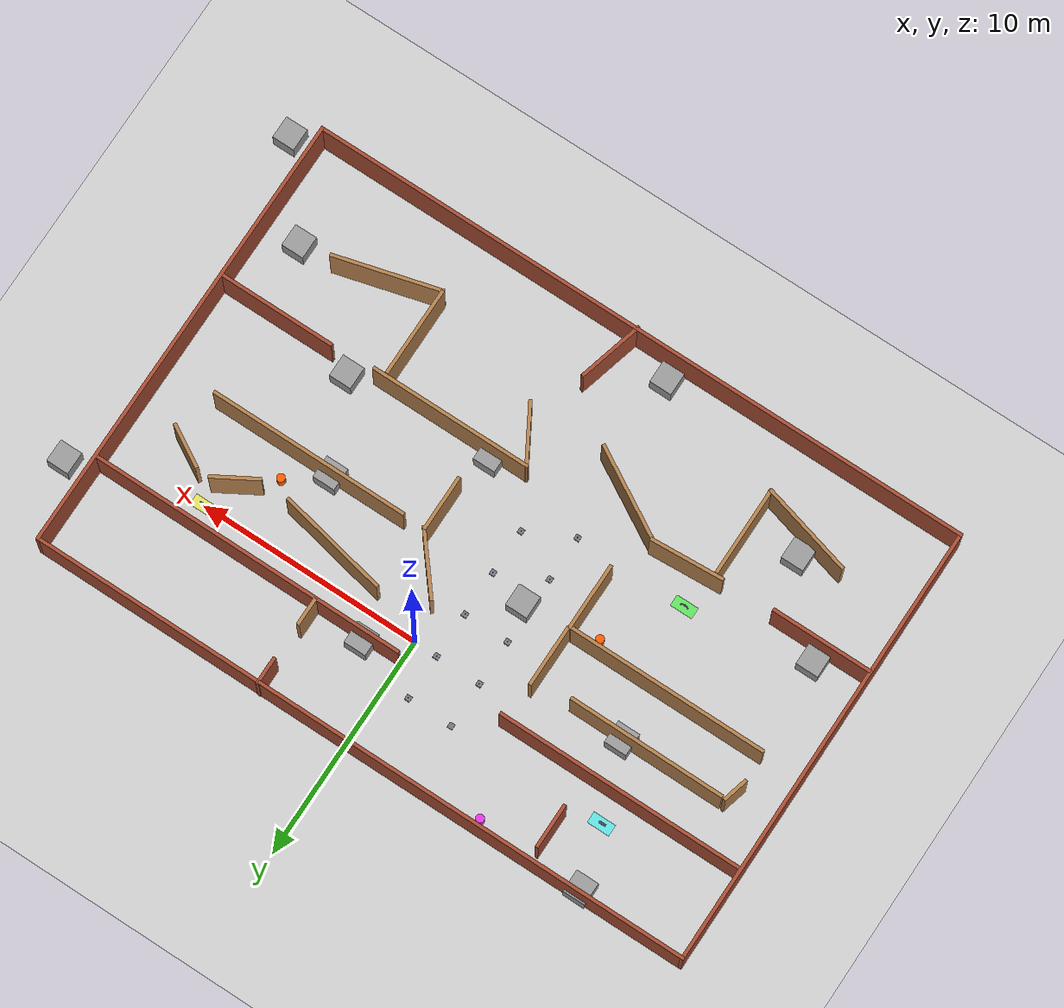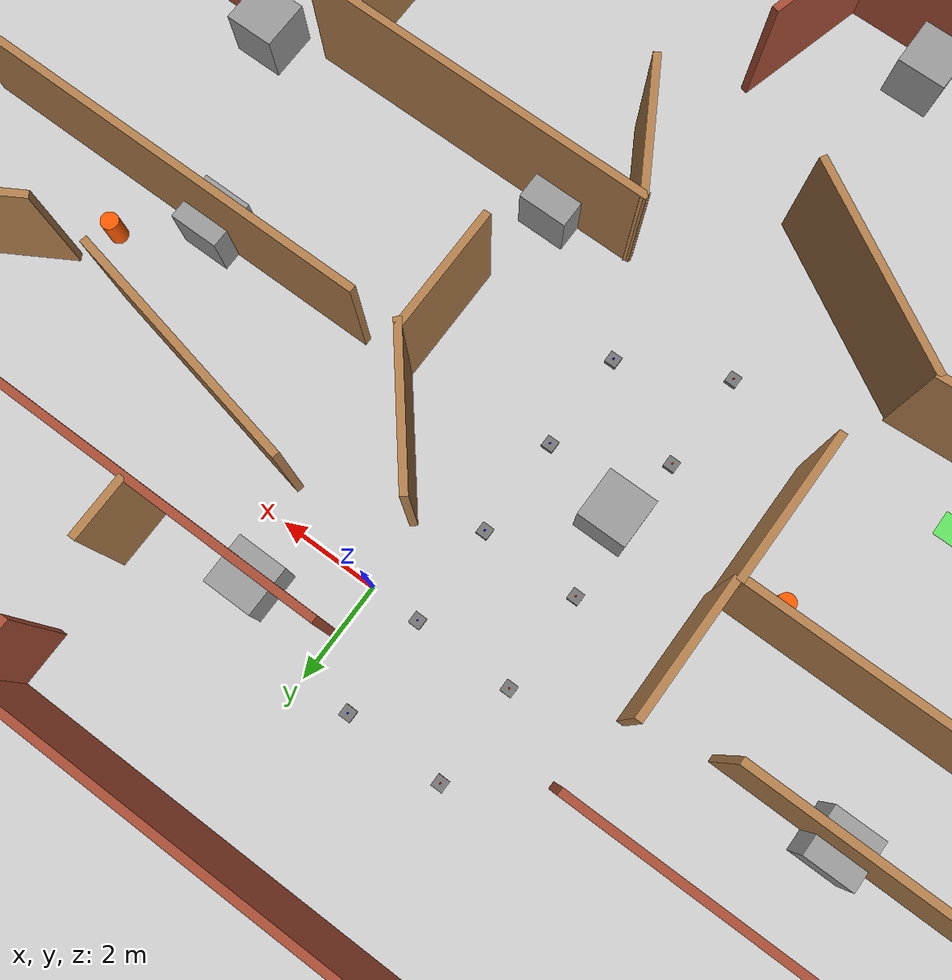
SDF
<sdf version='1.7'>
  <world name='my_world'>
    <model name='ground_plane'>
      <static>1</static>
      <link name='link'>
        <collision name='collision'>
          <geometry>
            <plane>
              <normal>0 0 1</normal>
              <size>100 100</size>
            </plane>
          </geometry>
          <surface>
            <contact>
              <collide_bitmask>65535</collide_bitmask>
              <ode/>
            </contact>
            <friction>
              <ode>
                <mu>100</mu>
                <mu2>50</mu2>
              </ode>
              <torsional>
                <ode/>
              </torsional>
            </friction>
            <bounce/>
          </surface>
          <max_contacts>10</max_contacts>
        </collision>
        <visual name='visual'>
          <cast_shadows>0</cast_shadows>
          <geometry>
            <plane>
              <normal>0 0 1</normal>
              <size>100 100</size>
            </plane>
          </geometry>
          <material>
            <script>
              <uri>file://media/materials/scripts/gazebo.material</uri>
              <name>Gazebo/Grey</name>
            </script>
          </material>
        </visual>
        <self_collide>0</self_collide>
        <enable_wind>0</enable_wind>
        <kinematic>0</kinematic>
      </link>
    </model>
    <light name='sun' type='directional'>
      <cast_shadows>1</cast_shadows>
      <pose>0 0 10 0 -0 0</pose>
      <diffuse>0.8 0.8 0.8 1</diffuse>
      <specular>0.2 0.2 0.2 1</specular>
      <attenuation>
        <range>1000</range>
        <constant>0.9</constant>
        <linear>0.01</linear>
        <quadratic>0.001</quadratic>
      </attenuation>
      <direction>-0.5 0.1 -0.9</direction>
      <spot>
        <inner_angle>0</inner_angle>
        <outer_angle>0</outer_angle>
        <falloff>0</falloff>
      </spot>
    </light>
    <model name='officeroom'>
      <pose>-0.693163 -4.92976 0 0 -0 0</pose>
      <link name='Wall_10'>
        <collision name='Wall_10_Collision'>
          <geometry>
            <box>
              <size>20 0.15 2.5</size>
            </box>
          </geometry>
          <pose>0 0 1.25 0 -0 0</pose>
          <max_contacts>10</max_contacts>
          <surface>
            <contact>
              <ode/>
            </contact>
            <bounce/>
            <friction>
              <torsional>
                <ode/>
              </torsional>
              <ode/>
            </friction>
          </surface>
        </collision>
        <visual name='Wall_10_Visual'>
          <pose>0 0 1.25 0 -0 0</pose>
          <geometry>
            <box>
              <size>20 0.15 2.5</size>
            </box>
          </geometry>
          <material>
            <script>
              <uri>file://media/materials/scripts/gazebo.material</uri>
              <name>Gazebo/Bricks</name>
            </script>
            <ambient>1 1 1 1</ambient>
          </material>
          <meta>
            <layer>0</layer>
          </meta>
        </visual>
        <pose>14.925 0.014919 0 0 -0 -1.57081</pose>
        <self_collide>0</self_collide>
        <enable_wind>0</enable_wind>
        <kinematic>0</kinematic>
      </link>
      <link name='Wall_107'>
        <collision name='Wall_107_Collision'>
          <geometry>
            <box>
              <size>3.27854 0.15 2.5</size>
            </box>
          </geometry>
          <pose>0 0 1.25 0 -0 0</pose>
          <max_contacts>10</max_contacts>
          <surface>
            <contact>
              <ode/>
            </contact>
            <bounce/>
            <friction>
              <torsional>
                <ode/>
              </torsional>
              <ode/>
            </friction>
          </surface>
        </collision>
        <visual name='Wall_107_Visual'>
          <pose>0 0 1.25 0 -0 0</pose>
          <geometry>
            <box>
              <size>3.27854 0.15 2.5</size>
            </box>
          </geometry>
          <material>
            <script>
              <uri>file://media/materials/scripts/gazebo.material</uri>
              <name>Gazebo/Wood</name>
            </script>
            <ambient>1 1 1 1</ambient>
          </material>
          <meta>
            <layer>0</layer>
          </meta>
        </visual>
        <pose>-6.58027 -3.242 0 0 -0 -3.08207</pose>
        <self_collide>0</self_collide>
        <enable_wind>0</enable_wind>
        <kinematic>0</kinematic>
      </link>
      <link name='Wall_109'>
        <collision name='Wall_109_Collision'>
          <geometry>
            <box>
              <size>4.5 0.15 2.5</size>
            </box>
          </geometry>
          <pose>0 0 1.25 0 -0 0</pose>
          <max_contacts>10</max_contacts>
          <surface>
            <contact>
              <ode/>
            </contact>
            <bounce/>
            <friction>
              <torsional>
                <ode/>
              </torsional>
              <ode/>
            </friction>
          </surface>
        </collision>
        <visual name='Wall_109_Visual'>
          <pose>0 0 1.25 0 -0 0</pose>
          <geometry>
            <box>
              <size>4.5 0.15 2.5</size>
            </box>
          </geometry>
          <material>
            <script>
              <uri>file://media/materials/scripts/gazebo.material</uri>
              <name>Gazebo/Bricks</name>
            </script>
            <ambient>1 1 1 1</ambient>
          </material>
          <meta>
            <layer>0</layer>
          </meta>
        </visual>
        <pose>-12.6881 -3.41033 0 0 -0 0</pose>
        <self_collide>0</self_collide>
        <enable_wind>0</enable_wind>
        <kinematic>0</kinematic>
      </link>
      <link name='Wall_113'>
        <collision name='Wall_113_Collision'>
          <geometry>
            <box>
              <size>7.25 0.15 2.5</size>
            </box>
          </geometry>
          <pose>0 0 1.25 0 -0 0</pose>
          <max_contacts>10</max_contacts>
          <surface>
            <contact>
              <ode/>
            </contact>
            <bounce/>
            <friction>
              <torsional>
                <ode/>
              </torsional>
              <ode/>
            </friction>
          </surface>
        </collision>
        <visual name='Wall_113_Visual'>
          <pose>0 0 1.25 0 -0 0</pose>
          <geometry>
            <box>
              <size>7.25 0.15 2.5</size>
            </box>
          </geometry>
          <material>
            <script>
              <uri>file://media/materials/scripts/gazebo.material</uri>
              <name>Gazebo/Wood</name>
            </script>
            <ambient>1 1 1 1</ambient>
          </material>
          <meta>
            <layer>0</layer>
          </meta>
        </visual>
        <pose>4.22386 -2.91887 0 0 -0 0</pose>
        <self_collide>0</self_collide>
        <enable_wind>0</enable_wind>
        <kinematic>0</kinematic>
      </link>
      <link name='Wall_115'>
        <collision name='Wall_115_Collision'>
          <geometry>
            <box>
              <size>5.25 0.15 2.5</size>
            </box>
          </geometry>
          <pose>0 0 1.25 0 -0 0</pose>
          <max_contacts>10</max_contacts>
          <surface>
            <contact>
              <ode/>
            </contact>
            <bounce/>
            <friction>
              <torsional>
                <ode/>
              </torsional>
              <ode/>
            </friction>
          </surface>
        </collision>
        <visual name='Wall_115_Visual'>
          <pose>0 0 1.25 0 -0 0</pose>
          <geometry>
            <box>
              <size>5.25 0.15 2.5</size>
            </box>
          </geometry>
          <material>
            <script>
              <uri>file://media/materials/scripts/gazebo.material</uri>
              <name>Gazebo/Bricks</name>
            </script>
            <ambient>1 1 1 1</ambient>
          </material>
          <meta>
            <layer>0</layer>
          </meta>
        </visual>
        <pose>12.3137 -2.7793 0 0 -0 3.14159</pose>
        <self_collide>0</self_collide>
        <enable_wind>0</enable_wind>
        <kinematic>0</kinematic>
      </link>
      <link name='Wall_118'>
        <collision name='Wall_118_Collision'>
          <geometry>
            <box>
              <size>2.5 0.15 2.5</size>
            </box>
          </geometry>
          <pose>0 0 1.25 0 -0 0</pose>
          <max_contacts>10</max_contacts>
          <surface>
            <contact>
              <ode/>
            </contact>
            <bounce/>
            <friction>
              <torsional>
                <ode/>
              </torsional>
              <ode/>
            </friction>
          </surface>
        </collision>
        <visual name='Wall_118_Visual'>
          <pose>0 0 1.25 0 -0 0</pose>
          <geometry>
            <box>
              <size>2.5 0.15 2.5</size>
            </box>
          </geometry>
          <material>
            <script>
              <uri>file://media/materials/scripts/gazebo.material</uri>
              <name>Gazebo/Wood</name>
            </script>
            <ambient>1 1 1 1</ambient>
          </material>
          <meta>
            <layer>0</layer>
          </meta>
        </visual>
        <pose>2.60295 0.147134 0 0 -0 -1.5708</pose>
        <self_collide>0</self_collide>
        <enable_wind>0</enable_wind>
        <kinematic>0</kinematic>
      </link>
      <link name='Wall_12'>
        <collision name='Wall_12_Collision'>
          <geometry>
            <box>
              <size>30 0.15 2.5</size>
            </box>
          </geometry>
          <pose>0 0 1.25 0 -0 0</pose>
          <max_contacts>10</max_contacts>
          <surface>
            <contact>
              <ode/>
            </contact>
            <bounce/>
            <friction>
              <torsional>
                <ode/>
              </torsional>
              <ode/>
            </friction>
          </surface>
        </collision>
        <visual name='Wall_12_Visual'>
          <pose>0 0 1.25 0 -0 0</pose>
          <geometry>
            <box>
              <size>30 0.15 2.5</size>
            </box>
          </geometry>
          <material>
            <script>
              <uri>file://media/materials/scripts/gazebo.material</uri>
              <name>Gazebo/Bricks</name>
            </script>
            <ambient>1 1 1 1</ambient>
          </material>
          <meta>
            <layer>0</layer>
          </meta>
        </visual>
        <pose>-0.000162 -9.90993 0 0 -0 3.14159</pose>
        <self_collide>0</self_collide>
        <enable_wind>0</enable_wind>
        <kinematic>0</kinematic>
      </link>
      <link name='Wall_120'>
        <collision name='Wall_120_Collision'>
          <geometry>
            <box>
              <size>2.75 0.15 2.5</size>
            </box>
          </geometry>
          <pose>0 0 1.25 0 -0 0</pose>
          <max_contacts>10</max_contacts>
          <surface>
            <contact>
              <ode/>
            </contact>
            <bounce/>
            <friction>
              <torsional>
                <ode/>
              </torsional>
              <ode/>
            </friction>
          </surface>
        </collision>
        <visual name='Wall_120_Visual'>
          <pose>0 0 1.25 0 -0 0</pose>
          <geometry>
            <box>
              <size>2.75 0.15 2.5</size>
            </box>
          </geometry>
          <material>
            <script>
              <uri>file://media/materials/scripts/gazebo.material</uri>
              <name>Gazebo/Wood</name>
            </script>
            <ambient>1 1 1 1</ambient>
          </material>
          <meta>
            <layer>0</layer>
          </meta>
        </visual>
        <pose>1.32386 -4.0447 0 0 -0 -1.0472</pose>
        <self_collide>0</self_collide>
        <enable_wind>0</enable_wind>
        <kinematic>0</kinematic>
      </link>
      <link name='Wall_125'>
        <collision name='Wall_125_Collision'>
          <geometry>
            <box>
              <size>4 0.15 2.5</size>
            </box>
          </geometry>
          <pose>0 0 1.25 0 -0 0</pose>
          <max_contacts>10</max_contacts>
          <surface>
            <contact>
              <ode/>
            </contact>
            <bounce/>
            <friction>
              <torsional>
                <ode/>
              </torsional>
              <ode/>
            </friction>
          </surface>
        </collision>
        <visual name='Wall_125_Visual'>
          <pose>0 0 1.25 0 -0 0</pose>
          <geometry>
            <box>
              <size>4 0.15 2.5</size>
            </box>
          </geometry>
          <material>
            <script>
              <uri>file://media/materials/scripts/gazebo.material</uri>
              <name>Gazebo/Wood</name>
            </script>
            <ambient>1 1 1 1</ambient>
          </material>
          <meta>
            <layer>0</layer>
          </meta>
        </visual>
        <pose>-7.82101 -5.406 0 0 -0 -1.5708</pose>
        <self_collide>0</self_collide>
        <enable_wind>0</enable_wind>
        <kinematic>0</kinematic>
      </link>
      <link name='Wall_127'>
        <collision name='Wall_127_Collision'>
          <geometry>
            <box>
              <size>4 0.15 2.5</size>
            </box>
          </geometry>
          <pose>0 0 1.25 0 -0 0</pose>
          <max_contacts>10</max_contacts>
          <surface>
            <contact>
              <ode/>
            </contact>
            <bounce/>
            <friction>
              <torsional>
                <ode/>
              </torsional>
              <ode/>
            </friction>
          </surface>
        </collision>
        <visual name='Wall_127_Visual'>
          <pose>0 0 1.25 0 -0 0</pose>
          <geometry>
            <box>
              <size>4 0.15 2.5</size>
            </box>
          </geometry>
          <material>
            <script>
              <uri>file://media/materials/scripts/gazebo.material</uri>
              <name>Gazebo/Wood</name>
            </script>
            <ambient>1 1 1 1</ambient>
          </material>
          <meta>
            <layer>0</layer>
          </meta>
        </visual>
        <pose>7.28181 -5.01384 0 0 -0 -1.5708</pose>
        <self_collide>0</self_collide>
        <enable_wind>0</enable_wind>
        <kinematic>0</kinematic>
      </link>
      <link name='Wall_129'>
        <collision name='Wall_129_Collision'>
          <geometry>
            <box>
              <size>4.25 0.15 2.5</size>
            </box>
          </geometry>
          <pose>0 0 1.25 0 -0 0</pose>
          <max_contacts>10</max_contacts>
          <surface>
            <contact>
              <ode/>
            </contact>
            <bounce/>
            <friction>
              <torsional>
                <ode/>
              </torsional>
              <ode/>
            </friction>
          </surface>
        </collision>
        <visual name='Wall_129_Visual'>
          <pose>0 0 1.25 0 -0 0</pose>
          <geometry>
            <box>
              <size>4.25 0.15 2.5</size>
            </box>
          </geometry>
          <material>
            <script>
              <uri>file://media/materials/scripts/gazebo.material</uri>
              <name>Gazebo/Wood</name>
            </script>
            <ambient>1 1 1 1</ambient>
          </material>
          <meta>
            <layer>0</layer>
          </meta>
        </visual>
        <pose>-9.80116 -6.80042 0 0 -0 2.87979</pose>
        <self_collide>0</self_collide>
        <enable_wind>0</enable_wind>
        <kinematic>0</kinematic>
      </link>
      <link name='Wall_132'>
        <collision name='Wall_132_Collision'>
          <geometry>
            <box>
              <size>4.75 0.15 2.5</size>
            </box>
          </geometry>
          <pose>0 0 1.25 0 -0 0</pose>
          <max_contacts>10</max_contacts>
          <surface>
            <contact>
              <ode/>
            </contact>
            <bounce/>
            <friction>
              <torsional>
                <ode/>
              </torsional>
              <ode/>
            </friction>
          </surface>
        </collision>
        <visual name='Wall_132_Visual'>
          <pose>0 0 1.25 0 -0 0</pose>
          <geometry>
            <box>
              <size>4.75 0.15 2.5</size>
            </box>
          </geometry>
          <material>
            <script>
              <uri>file://media/materials/scripts/gazebo.material</uri>
              <name>Gazebo/Wood</name>
            </script>
            <ambient>1 1 1 1</ambient>
          </material>
          <meta>
            <layer>0</layer>
          </meta>
        </visual>
        <pose>9.51735 -6.40461 0 0 -0 0.261799</pose>
        <self_collide>0</self_collide>
        <enable_wind>0</enable_wind>
        <kinematic>0</kinematic>
      </link>
      <link name='Wall_134'>
        <collision name='Wall_134_Collision'>
          <geometry>
            <box>
              <size>3 0.15 2.5</size>
            </box>
          </geometry>
          <pose>0 0 1.25 0 -0 0</pose>
          <max_contacts>10</max_contacts>
          <surface>
            <contact>
              <ode/>
            </contact>
            <bounce/>
            <friction>
              <torsional>
                <ode/>
              </torsional>
              <ode/>
            </friction>
          </surface>
        </collision>
        <visual name='Wall_134_Visual'>
          <pose>0 0 1.25 0 -0 0</pose>
          <geometry>
            <box>
              <size>3 0.15 2.5</size>
            </box>
          </geometry>
          <material>
            <script>
              <uri>file://media/materials/scripts/gazebo.material</uri>
              <name>Gazebo/Bricks</name>
            </script>
            <ambient>1 1 1 1</ambient>
          </material>
          <meta>
            <layer>0</layer>
          </meta>
        </visual>
        <pose>0.445972 -8.57754 0 0 -0 1.309</pose>
        <self_collide>0</self_collide>
        <enable_wind>0</enable_wind>
        <kinematic>0</kinematic>
      </link>
      <link name='Wall_15'>
        <collision name='Wall_15_Collision'>
          <geometry>
            <box>
              <size>20 0.15 2.5</size>
            </box>
          </geometry>
          <pose>0 0 1.25 0 -0 0</pose>
          <max_contacts>10</max_contacts>
          <surface>
            <contact>
              <ode/>
            </contact>
            <bounce/>
            <friction>
              <torsional>
                <ode/>
              </torsional>
              <ode/>
            </friction>
          </surface>
        </collision>
        <visual name='Wall_15_Visual'>
          <pose>0 0 1.25 0 -0 0</pose>
          <geometry>
            <box>
              <size>20 0.15 2.5</size>
            </box>
          </geometry>
          <material>
            <script>
              <uri>file://media/materials/scripts/gazebo.material</uri>
              <name>Gazebo/Bricks</name>
            </script>
            <ambient>1 1 1 1</ambient>
          </material>
          <meta>
            <layer>0</layer>
          </meta>
        </visual>
        <pose>-14.9252 0.015073 0 0 -0 1.5708</pose>
        <self_collide>0</self_collide>
        <enable_wind>0</enable_wind>
        <kinematic>0</kinematic>
      </link>
      <link name='Wall_2'>
        <collision name='Wall_2_Collision'>
          <geometry>
            <box>
              <size>30 0.15 2.5</size>
            </box>
          </geometry>
          <pose>0 0 1.25 0 -0 0</pose>
          <max_contacts>10</max_contacts>
          <surface>
            <contact>
              <ode/>
            </contact>
            <bounce/>
            <friction>
              <torsional>
                <ode/>
              </torsional>
              <ode/>
            </friction>
          </surface>
        </collision>
        <visual name='Wall_2_Visual'>
          <pose>0 0 1.25 0 -0 0</pose>
          <geometry>
            <box>
              <size>30 0.15 2.5</size>
            </box>
          </geometry>
          <material>
            <script>
              <uri>file://media/materials/scripts/gazebo.material</uri>
              <name>Gazebo/Bricks</name>
            </script>
            <ambient>1 1 1 1</ambient>
          </material>
          <meta>
            <layer>0</layer>
          </meta>
        </visual>
        <pose>0.000163 9.93976 0 0 -0 0</pose>
        <self_collide>0</self_collide>
        <enable_wind>0</enable_wind>
        <kinematic>0</kinematic>
      </link>
      <link name='Wall_29'>
        <collision name='Wall_29_Collision'>
          <geometry>
            <box>
              <size>1.25 0.15 2.5</size>
            </box>
          </geometry>
          <pose>0 0 1.25 0 -0 0</pose>
          <max_contacts>10</max_contacts>
          <surface>
            <contact>
              <ode/>
            </contact>
            <bounce/>
            <friction>
              <torsional>
                <ode/>
              </torsional>
              <ode/>
            </friction>
          </surface>
        </collision>
        <visual name='Wall_29_Visual'>
          <pose>0 0 1.25 0 -0 0</pose>
          <geometry>
            <box>
              <size>1.25 0.15 2.5</size>
            </box>
          </geometry>
          <material>
            <script>
              <uri>file://media/materials/scripts/gazebo.material</uri>
              <name>Gazebo/Bricks</name>
            </script>
            <ambient>1 1 1 1</ambient>
          </material>
          <meta>
            <layer>0</layer>
          </meta>
        </visual>
        <pose>4.61028 9.42084 0 0 -0 -1.5708</pose>
        <self_collide>0</self_collide>
        <enable_wind>0</enable_wind>
        <kinematic>0</kinematic>
      </link>
      <link name='Wall_31'>
        <collision name='Wall_31_Collision'>
          <geometry>
            <box>
              <size>1.25 0.15 2.5</size>
            </box>
          </geometry>
          <pose>0 0 1.25 0 -0 0</pose>
          <max_contacts>10</max_contacts>
          <surface>
            <contact>
              <ode/>
            </contact>
            <bounce/>
            <friction>
              <torsional>
                <ode/>
              </torsional>
              <ode/>
            </friction>
          </surface>
        </collision>
        <visual name='Wall_31_Visual'>
          <pose>0 0 1.25 0 -0 0</pose>
          <geometry>
            <box>
              <size>1.25 0.15 2.5</size>
            </box>
          </geometry>
          <material>
            <script>
              <uri>file://media/materials/scripts/gazebo.material</uri>
              <name>Gazebo/Wood</name>
            </script>
            <ambient>1 1 1 1</ambient>
          </material>
          <meta>
            <layer>0</layer>
          </meta>
        </visual>
        <pose>4.59016 6.61881 0 0 -0 1.5708</pose>
        <self_collide>0</self_collide>
        <enable_wind>0</enable_wind>
        <kinematic>0</kinematic>
      </link>
      <link name='Wall_34'>
        <collision name='Wall_34_Collision'>
          <geometry>
            <box>
              <size>2 0.15 2.5</size>
            </box>
          </geometry>
          <pose>0 0 1.25 0 -0 0</pose>
          <max_contacts>10</max_contacts>
          <surface>
            <contact>
              <ode/>
            </contact>
            <bounce/>
            <friction>
              <torsional>
                <ode/>
              </torsional>
              <ode/>
            </friction>
          </surface>
        </collision>
        <visual name='Wall_34_Visual'>
          <pose>0 0 1.25 0 -0 0</pose>
          <geometry>
            <box>
              <size>2 0.15 2.5</size>
            </box>
          </geometry>
          <material>
            <script>
              <uri>file://media/materials/scripts/gazebo.material</uri>
              <name>Gazebo/Bricks</name>
            </script>
            <ambient>1 1 1 1</ambient>
          </material>
          <meta>
            <layer>0</layer>
          </meta>
        </visual>
        <pose>-7.92097 8.43964 0 0 -0 -1.5708</pose>
        <self_collide>0</self_collide>
        <enable_wind>0</enable_wind>
        <kinematic>0</kinematic>
      </link>
      <link name='Wall_38'>
        <collision name='Wall_38_Collision'>
          <geometry>
            <box>
              <size>11 0.15 2.5</size>
            </box>
          </geometry>
          <pose>0 0 1.25 0 -0 0</pose>
          <max_contacts>10</max_contacts>
          <surface>
            <contact>
              <ode/>
            </contact>
            <bounce/>
            <friction>
              <torsional>
                <ode/>
              </torsional>
              <ode/>
            </friction>
          </surface>
        </collision>
        <visual name='Wall_38_Visual'>
          <pose>0 0 1.25 0 -0 0</pose>
          <geometry>
            <box>
              <size>11 0.15 2.5</size>
            </box>
          </geometry>
          <material>
            <script>
              <uri>file://media/materials/scripts/gazebo.material</uri>
              <name>Gazebo/Bricks</name>
            </script>
            <ambient>1 1 1 1</ambient>
          </material>
          <meta>
            <layer>0</layer>
          </meta>
        </visual>
        <pose>-9.35541 5.8262 0 0 -0 0</pose>
        <self_collide>0</self_collide>
        <enable_wind>0</enable_wind>
        <kinematic>0</kinematic>
      </link>
      <link name='Wall_40'>
        <collision name='Wall_40_Collision'>
          <geometry>
            <box>
              <size>14.25 0.15 2.5</size>
            </box>
          </geometry>
          <pose>0 0 1.25 0 -0 0</pose>
          <max_contacts>10</max_contacts>
          <surface>
            <contact>
              <ode/>
            </contact>
            <bounce/>
            <friction>
              <torsional>
                <ode/>
              </torsional>
              <ode/>
            </friction>
          </surface>
        </collision>
        <visual name='Wall_40_Visual'>
          <pose>0 0 1.25 0 -0 0</pose>
          <geometry>
            <box>
              <size>14.25 0.15 2.5</size>
            </box>
          </geometry>
          <material>
            <script>
              <uri>file://media/materials/scripts/gazebo.material</uri>
              <name>Gazebo/Bricks</name>
            </script>
            <ambient>1 1 1 1</ambient>
          </material>
          <meta>
            <layer>0</layer>
          </meta>
        </visual>
        <pose>7.83962 5.98375 0 0 -0 3.14159</pose>
        <self_collide>0</self_collide>
        <enable_wind>0</enable_wind>
        <kinematic>0</kinematic>
      </link>
      <link name='Wall_46'>
        <collision name='Wall_46_Collision'>
          <geometry>
            <box>
              <size>7.0 0.15 2.5</size>
            </box>
          </geometry>
          <pose>0 0 1.25 0 -0 0</pose>
          <max_contacts>10</max_contacts>
          <surface>
            <contact>
              <ode/>
            </contact>
            <bounce/>
            <friction>
              <torsional>
                <ode/>
              </torsional>
              <ode/>
            </friction>
          </surface>
        </collision>
        <visual name='Wall_46_Visual'>
          <pose>0 0 1.25 0 -0 0</pose>
          <geometry>
            <box>
              <size>7.0 0.15 2.5</size>
            </box>
          </geometry>
          <material>
            <script>
              <uri>file://media/materials/scripts/gazebo.material</uri>
              <name>Gazebo/Wood</name>
            </script>
            <ambient>1 1 1 1</ambient>
          </material>
          <meta>
            <layer>0</layer>
          </meta>
        </visual>
        <pose>-9.30884 3.8355 0 0 -0 -0.004163</pose>
        <self_collide>0</self_collide>
        <enable_wind>0</enable_wind>
        <kinematic>0</kinematic>
      </link>
      <link name='Wall_49'>
        <collision name='Wall_49_Collision'>
          <geometry>
            <box>
              <size>1.17019 0.15 2.5</size>
            </box>
          </geometry>
          <pose>0 0 1.25 0 -0 0</pose>
          <max_contacts>10</max_contacts>
          <surface>
            <contact>
              <ode/>
            </contact>
            <bounce/>
            <friction>
              <torsional>
                <ode/>
              </torsional>
              <ode/>
            </friction>
          </surface>
        </collision>
        <visual name='Wall_49_Visual'>
          <pose>0 0 1.25 0 -0 0</pose>
          <geometry>
            <box>
              <size>1.17019 0.15 2.5</size>
            </box>
          </geometry>
          <material>
            <script>
              <uri>file://media/materials/scripts/gazebo.material</uri>
              <name>Gazebo/Wood</name>
            </script>
            <ambient>1 1 1 1</ambient>
          </material>
          <meta>
            <layer>0</layer>
          </meta>
        </visual>
        <pose>-13.076 3.35727 0 0 -0 -1.82702</pose>
        <self_collide>0</self_collide>
        <enable_wind>0</enable_wind>
        <kinematic>0</kinematic>
      </link>
      <link name='Wall_57'>
        <collision name='Wall_57_Collision'>
          <geometry>
            <box>
              <size>2.75 0.15 2.5</size>
            </box>
          </geometry>
          <pose>0 0 1.25 0 -0 0</pose>
          <max_contacts>10</max_contacts>
          <surface>
            <contact>
              <ode/>
            </contact>
            <bounce/>
            <friction>
              <torsional>
                <ode/>
              </torsional>
              <ode/>
            </friction>
          </surface>
        </collision>
        <visual name='Wall_57_Visual'>
          <pose>0 0 1.25 0 -0 0</pose>
          <geometry>
            <box>
              <size>2.75 0.15 2.5</size>
            </box>
          </geometry>
          <material>
            <script>
              <uri>file://media/materials/scripts/gazebo.material</uri>
              <name>Gazebo/Wood</name>
            </script>
            <ambient>1 1 1 1</ambient>
          </material>
          <meta>
            <layer>0</layer>
          </meta>
        </visual>
        <pose>-4.21161 2.89682 0 0 -0 1.5708</pose>
        <self_collide>0</self_collide>
        <enable_wind>0</enable_wind>
        <kinematic>0</kinematic>
      </link>
      <link name='Wall_59'>
        <collision name='Wall_59_Collision'>
          <geometry>
            <box>
              <size>5.0 0.15 2.5</size>
            </box>
          </geometry>
          <pose>0 0 1.25 0 -0 0</pose>
          <max_contacts>10</max_contacts>
          <surface>
            <contact>
              <ode/>
            </contact>
            <bounce/>
            <friction>
              <torsional>
                <ode/>
              </torsional>
              <ode/>
            </friction>
          </surface>
        </collision>
        <visual name='Wall_59_Visual'>
          <pose>0 0 1.25 0 -0 0</pose>
          <geometry>
            <box>
              <size>5.0 0.15 2.5</size>
            </box>
          </geometry>
          <material>
            <script>
              <uri>file://media/materials/scripts/gazebo.material</uri>
              <name>Gazebo/Wood</name>
            </script>
            <ambient>1 1 1 1</ambient>
          </material>
          <meta>
            <layer>0</layer>
          </meta>
        </visual>
        <pose>5.28704 3.77735 0 0 -0 -0.202428</pose>
        <self_collide>0</self_collide>
        <enable_wind>0</enable_wind>
        <kinematic>0</kinematic>
      </link>
      <link name='Wall_60'>
        <collision name='Wall_60_Collision'>
          <geometry>
            <box>
              <size>2.1 0.15 2.5</size>
            </box>
          </geometry>
          <pose>0 0 1.25 0 -0 0</pose>
          <max_contacts>10</max_contacts>
          <surface>
            <contact>
              <ode/>
            </contact>
            <bounce/>
            <friction>
              <torsional>
                <ode/>
              </torsional>
              <ode/>
            </friction>
          </surface>
        </collision>
        <visual name='Wall_60_Visual'>
          <pose>0 0 1.25 0 -0 0</pose>
          <geometry>
            <box>
              <size>2.1 0.15 2.5</size>
            </box>
          </geometry>
          <material>
            <script>
              <uri>file://media/materials/scripts/gazebo.material</uri>
              <name>Gazebo/Wood</name>
            </script>
            <ambient>1 1 1 1</ambient>
          </material>
          <meta>
            <layer>0</layer>
          </meta>
        </visual>
        <pose>9.88652 3.73459 0 0 -0 0.527727</pose>
        <self_collide>0</self_collide>
        <enable_wind>0</enable_wind>
        <kinematic>0</kinematic>
      </link>
      <link name='Wall_61'>
        <collision name='Wall_61_Collision'>
          <geometry>
            <box>
              <size>2.0 0.15 2.5</size>
            </box>
          </geometry>
          <pose>0 0 1.25 0 -0 0</pose>
          <max_contacts>10</max_contacts>
          <surface>
            <contact>
              <ode/>
            </contact>
            <bounce/>
            <friction>
              <torsional>
                <ode/>
              </torsional>
              <ode/>
            </friction>
          </surface>
        </collision>
        <visual name='Wall_61_Visual'>
          <pose>0 0 1.25 0 -0 0</pose>
          <geometry>
            <box>
              <size>2.0 0.15 2.5</size>
            </box>
          </geometry>
          <material>
            <script>
              <uri>file://media/materials/scripts/gazebo.material</uri>
              <name>Gazebo/Wood</name>
            </script>
            <ambient>1 1 1 1</ambient>
          </material>
          <meta>
            <layer>0</layer>
          </meta>
        </visual>
        <pose>12.2003 3.7238 0 0 -0 -0.523599</pose>
        <self_collide>0</self_collide>
        <enable_wind>0</enable_wind>
        <kinematic>0</kinematic>
      </link>
      <link name='Wall_66'>
        <collision name='Wall_66_Collision'>
          <geometry>
            <box>
              <size>3.01901 0.15 2.5</size>
            </box>
          </geometry>
          <pose>0 0 1.25 0 -0 0</pose>
          <max_contacts>10</max_contacts>
          <surface>
            <contact>
              <ode/>
            </contact>
            <bounce/>
            <friction>
              <torsional>
                <ode/>
              </torsional>
              <ode/>
            </friction>
          </surface>
        </collision>
        <visual name='Wall_66_Visual'>
          <pose>0 0 1.25 0 -0 0</pose>
          <geometry>
            <box>
              <size>3.01901 0.15 2.5</size>
            </box>
          </geometry>
          <material>
            <script>
              <uri>file://media/materials/scripts/gazebo.material</uri>
              <name>Gazebo/Wood</name>
            </script>
            <ambient>1 1 1 1</ambient>
          </material>
          <meta>
            <layer>0</layer>
          </meta>
        </visual>
        <pose>1.74226 2.43334 0 0 -0 2.25548</pose>
        <self_collide>0</self_collide>
        <enable_wind>0</enable_wind>
        <kinematic>0</kinematic>
      </link>
      <link name='Wall_68'>
        <collision name='Wall_68_Collision'>
          <geometry>
            <box>
              <size>9 0.15 2.5</size>
            </box>
          </geometry>
          <pose>0 0 1.25 0 -0 0</pose>
          <max_contacts>10</max_contacts>
          <surface>
            <contact>
              <ode/>
            </contact>
            <bounce/>
            <friction>
              <torsional>
                <ode/>
              </torsional>
              <ode/>
            </friction>
          </surface>
        </collision>
        <visual name='Wall_68_Visual'>
          <pose>0 0 1.25 0 -0 0</pose>
          <geometry>
            <box>
              <size>9 0.15 2.5</size>
            </box>
          </geometry>
          <material>
            <script>
              <uri>file://media/materials/scripts/gazebo.material</uri>
              <name>Gazebo/Wood</name>
            </script>
            <ambient>1 1 1 1</ambient>
          </material>
          <meta>
            <layer>0</layer>
          </meta>
        </visual>
        <pose>-8.68528 1.49923 0 0 -0 3.14159</pose>
        <self_collide>0</self_collide>
        <enable_wind>0</enable_wind>
        <kinematic>0</kinematic>
      </link>
      <link name='Wall_72'>
        <collision name='Wall_72_Collision'>
          <geometry>
            <box>
              <size>8.9356 0.15 2.5</size>
            </box>
          </geometry>
          <pose>0 0 1.25 0 -0 0</pose>
          <max_contacts>10</max_contacts>
          <surface>
            <contact>
              <ode/>
            </contact>
            <bounce/>
            <friction>
              <torsional>
                <ode/>
              </torsional>
              <ode/>
            </friction>
          </surface>
        </collision>
        <visual name='Wall_72_Visual'>
          <pose>0 0 1.25 0 -0 0</pose>
          <geometry>
            <box>
              <size>8.9356 0.15 2.5</size>
            </box>
          </geometry>
          <material>
            <script>
              <uri>file://media/materials/scripts/gazebo.material</uri>
              <name>Gazebo/Wood</name>
            </script>
            <ambient>1 1 1 1</ambient>
          </material>
          <meta>
            <layer>0</layer>
          </meta>
        </visual>
        <pose>8.04226 1.32213 0 0 -0 3.14159</pose>
        <self_collide>0</self_collide>
        <enable_wind>0</enable_wind>
        <kinematic>0</kinematic>
      </link>
      <link name='Wall_75'>
        <collision name='Wall_75_Collision'>
          <geometry>
            <box>
              <size>3 0.15 2.5</size>
            </box>
          </geometry>
          <pose>0 0 1.25 0 -0 0</pose>
          <max_contacts>10</max_contacts>
          <surface>
            <contact>
              <ode/>
            </contact>
            <bounce/>
            <friction>
              <torsional>
                <ode/>
              </torsional>
              <ode/>
            </friction>
          </surface>
        </collision>
        <visual name='Wall_75_Visual'>
          <pose>0 0 1.25 0 -0 0</pose>
          <geometry>
            <box>
              <size>3 0.15 2.5</size>
            </box>
          </geometry>
          <material>
            <script>
              <uri>file://media/materials/scripts/gazebo.material</uri>
              <name>Gazebo/Wood</name>
            </script>
            <ambient>1 1 1 1</ambient>
          </material>
          <meta>
            <layer>0</layer>
          </meta>
        </visual>
        <pose>-4.26028 0.074229 0 0 -0 -1.5708</pose>
        <self_collide>0</self_collide>
        <enable_wind>0</enable_wind>
        <kinematic>0</kinematic>
      </link>
      <link name='Wall_81'>
        <collision name='Wall_81_Collision'>
          <geometry>
            <box>
              <size>4.25 0.15 2.5</size>
            </box>
          </geometry>
          <pose>0 0 1.25 0 -0 0</pose>
          <max_contacts>10</max_contacts>
          <surface>
            <contact>
              <ode/>
            </contact>
            <bounce/>
            <friction>
              <torsional>
                <ode/>
              </torsional>
              <ode/>
            </friction>
          </surface>
        </collision>
        <visual name='Wall_81_Visual'>
          <pose>0 0 1.25 0 -0 0</pose>
          <geometry>
            <box>
              <size>4.25 0.15 2.5</size>
            </box>
          </geometry>
          <material>
            <script>
              <uri>file://media/materials/scripts/gazebo.material</uri>
              <name>Gazebo/Wood</name>
            </script>
            <ambient>1 1 1 1</ambient>
          </material>
          <meta>
            <layer>0</layer>
          </meta>
        </visual>
        <pose>-3.1969 -4.22048 0 0 -0 -0.523599</pose>
        <self_collide>0</self_collide>
        <enable_wind>0</enable_wind>
        <kinematic>0</kinematic>
      </link>
      <static>1</static>
    </model>
    <gravity>0 0 -9.8</gravity>
    <magnetic_field>6e-06 2.3e-05 -4.2e-05</magnetic_field>
    <atmosphere type='adiabatic'/>
    <physics type='ode'>
      <max_step_size>0.002</max_step_size>
      <real_time_factor>1</real_time_factor>
      <real_time_update_rate>500</real_time_update_rate>
    </physics>
    <scene>
      <ambient>0.4 0.4 0.4 1</ambient>
      <background>0.7 0.7 0.7 1</background>
      <shadows>1</shadows>
    </scene>
    <audio>
      <device>default</device>
    </audio>
    <wind/>
    <spherical_coordinates>
      <surface_model>EARTH_WGS84</surface_model>
      <latitude_deg>0</latitude_deg>
      <longitude_deg>0</longitude_deg>
      <elevation>0</elevation>
      <heading_deg>0</heading_deg>
    </spherical_coordinates>
    <!-- Ignore the editor's stale runtime snapshot. It relocated the three
         delivery zones to (5, -11..-13), overriding their model poses. -->
    <model name='competition_red_pickup_tray'>
      <static>true</static>
      <pose>-3 -2 0.05 0 0 1.57079632679</pose>
      <link name='tray'>
        <collision name='collision'>
          <geometry><box><size>0.24 0.24 0.10</size></box></geometry>
          <surface><friction><ode><mu>10</mu><mu2>10</mu2></ode></friction></surface>
        </collision>
        <visual name='visual'>
          <geometry><box><size>0.24 0.24 0.10</size></box></geometry>
          <material><ambient>0.35 0.35 0.35 1</ambient><diffuse>0.45 0.45 0.45 1</diffuse></material>
        </visual>
      </link>
    </model>
    <model name='competition_red_pickup_tray_2'>
      <static>true</static>
      <pose>-3 -5 0.05 0 0 1.57079632679</pose>
      <link name='tray'>
        <collision name='collision'>
          <geometry><box><size>0.24 0.24 0.10</size></box></geometry>
          <surface><friction><ode><mu>10</mu><mu2>10</mu2></ode></friction></surface>
        </collision>
        <visual name='visual'>
          <geometry><box><size>0.24 0.24 0.10</size></box></geometry>
          <material><ambient>0.35 0.35 0.35 1</ambient><diffuse>0.45 0.45 0.45 1</diffuse></material>
        </visual>
      </link>
    </model>
    <model name='competition_red_pickup_tray_3'>
      <static>true</static>
      <pose>-3 0 0.05 0 0 1.57079632679</pose>
      <link name='tray'>
        <collision name='collision'>
          <geometry><box><size>0.24 0.24 0.10</size></box></geometry>
          <surface><friction><ode><mu>10</mu><mu2>10</mu2></ode></friction></surface>
        </collision>
        <visual name='visual'>
          <geometry><box><size>0.24 0.24 0.10</size></box></geometry>
          <material><ambient>0.35 0.35 0.35 1</ambient><diffuse>0.45 0.45 0.45 1</diffuse></material>
        </visual>
      </link>
    </model>
    <model name='competition_red_pickup_tray_4'>
      <static>true</static>
      <pose>-3 2 0.05 0 0 1.57079632679</pose>
      <link name='tray'>
        <collision name='collision'>
          <geometry><box><size>0.24 0.24 0.10</size></box></geometry>
          <surface><friction><ode><mu>10</mu><mu2>10</mu2></ode></friction></surface>
        </collision>
        <visual name='visual'>
          <geometry><box><size>0.24 0.24 0.10</size></box></geometry>
          <material><ambient>0.35 0.35 0.35 1</ambient><diffuse>0.45 0.45 0.45 1</diffuse></material>
        </visual>
      </link>
    </model>
    <model name='competition_red_pickup_tray_5'>
      <static>true</static>
      <pose>-3 -7 0.05 0 0 1.57079632679</pose>
      <link name='tray'>
        <collision name='collision'>
          <geometry><box><size>0.24 0.24 0.10</size></box></geometry>
          <surface><friction><ode><mu>10</mu><mu2>10</mu2></ode></friction></surface>
        </collision>
        <visual name='visual'>
          <geometry><box><size>0.24 0.24 0.10</size></box></geometry>
          <material><ambient>0.35 0.35 0.35 1</ambient><diffuse>0.45 0.45 0.45 1</diffuse></material>
        </visual>
      </link>
    </model>
    <model name='competition_blue_pickup_tray'>
      <static>true</static>
      <pose>-1 -2 0.05 0 0 1.57079632679</pose>
      <link name='tray'>
        <collision name='collision'>
          <geometry><box><size>0.24 0.24 0.10</size></box></geometry>
          <surface><friction><ode><mu>10</mu><mu2>10</mu2></ode></friction></surface>
        </collision>
        <visual name='visual'>
          <geometry><box><size>0.24 0.24 0.10</size></box></geometry>
          <material><ambient>0.35 0.35 0.35 1</ambient><diffuse>0.45 0.45 0.45 1</diffuse></material>
        </visual>
      </link>
    </model>
    <model name='competition_blue_pickup_tray_2'>
      <static>true</static>
      <pose>-1 -4 0.05 0 0 1.57079632679</pose>
      <link name='tray'>
        <collision name='collision'>
          <geometry><box><size>0.24 0.24 0.10</size></box></geometry>
          <surface><friction><ode><mu>10</mu><mu2>10</mu2></ode></friction></surface>
        </collision>
        <visual name='visual'>
          <geometry><box><size>0.24 0.24 0.10</size></box></geometry>
          <material><ambient>0.35 0.35 0.35 1</ambient><diffuse>0.45 0.45 0.45 1</diffuse></material>
        </visual>
      </link>
    </model>
    <model name='competition_blue_pickup_tray_3'>
      <static>true</static>
      <pose>-1 0 0.05 0 0 1.57079632679</pose>
      <link name='tray'>
        <collision name='collision'>
          <geometry><box><size>0.24 0.24 0.10</size></box></geometry>
          <surface><friction><ode><mu>10</mu><mu2>10</mu2></ode></friction></surface>
        </collision>
        <visual name='visual'>
          <geometry><box><size>0.24 0.24 0.10</size></box></geometry>
          <material><ambient>0.35 0.35 0.35 1</ambient><diffuse>0.45 0.45 0.45 1</diffuse></material>
        </visual>
      </link>
    </model>
    <model name='competition_blue_pickup_tray_4'>
      <static>true</static>
      <pose>-1 2 0.05 0 0 1.57079632679</pose>
      <link name='tray'>
        <collision name='collision'>
          <geometry><box><size>0.24 0.24 0.10</size></box></geometry>
          <surface><friction><ode><mu>10</mu><mu2>10</mu2></ode></friction></surface>
        </collision>
        <visual name='visual'>
          <geometry><box><size>0.24 0.24 0.10</size></box></geometry>
          <material><ambient>0.35 0.35 0.35 1</ambient><diffuse>0.45 0.45 0.45 1</diffuse></material>
        </visual>
      </link>
    </model>
    <model name='competition_blue_pickup_tray_5'>
      <static>true</static>
      <pose>-1 -6 0.05 0 0 1.57079632679</pose>
      <link name='tray'>
        <collision name='collision'>
          <geometry><box><size>0.24 0.24 0.10</size></box></geometry>
          <surface><friction><ode><mu>10</mu><mu2>10</mu2></ode></friction></surface>
        </collision>
        <visual name='visual'>
          <geometry><box><size>0.24 0.24 0.10</size></box></geometry>
          <material><ambient>0.35 0.35 0.35 1</ambient><diffuse>0.45 0.45 0.45 1</diffuse></material>
        </visual>
      </link>
    </model>
    <model name='red_cube_1'>
      <pose>-3 -2 0.13 0 -0 0</pose>
      <link name='link'>
        <inertial>
          <mass>0.005</mass>
          <pose>0 0 0 0 -0 0</pose>
          <inertia>
            <ixx>0.00000075</ixx>
            <ixy>0</ixy>
            <ixz>0</ixz>
            <iyy>0.00000075</iyy>
            <iyz>0</iyz>
            <izz>0.00000075</izz>
          </inertia>
        </inertial>
        <collision name='collision'>
          <geometry>
            <box>
              <size>0.03 0.03 0.03</size>
            </box>
          </geometry>
          <max_contacts>10</max_contacts>
          <surface>
            <contact>
              <ode>
                <soft_cfm>0.001</soft_cfm>
                <soft_erp>0.2</soft_erp>
                <max_vel>0.1</max_vel>
                <min_depth>0.001</min_depth>
              </ode>
            </contact>
            <bounce/>
            <friction>
              <ode>
                <mu>0.01</mu>
                <mu2>0.01</mu2>
              </ode>
              <torsional>
                <ode/>
              </torsional>
            </friction>
          </surface>
        </collision>
        <visual name='visual'>
          <geometry>
            <box>
              <size>0.03 0.03 0.03</size>
            </box>
          </geometry>
          <material>
            <ambient>1 0 0 1</ambient>
            <diffuse>1 0 0 1</diffuse>
          </material>
        </visual>
        <self_collide>0</self_collide>
        <enable_wind>0</enable_wind>
        <kinematic>0</kinematic>
      </link>
    </model>
    <model name='red_cube_2'>
      <pose>-3 -5 0.13 0 -0 0</pose>
      <link name='link'>
        <inertial>
          <mass>0.005</mass>
          <pose>0 0 0 0 -0 0</pose>
          <inertia>
            <ixx>0.00000075</ixx>
            <ixy>0</ixy>
            <ixz>0</ixz>
            <iyy>0.00000075</iyy>
            <iyz>0</iyz>
            <izz>0.00000075</izz>
          </inertia>
        </inertial>
        <collision name='collision'>
          <geometry>
            <box>
              <size>0.03 0.03 0.03</size>
            </box>
          </geometry>
          <max_contacts>10</max_contacts>
          <surface>
            <contact>
              <ode>
                <soft_cfm>0.001</soft_cfm>
                <soft_erp>0.2</soft_erp>
                <max_vel>0.1</max_vel>
                <min_depth>0.001</min_depth>
              </ode>
            </contact>
            <bounce/>
            <friction>
              <ode>
                <mu>0.01</mu>
                <mu2>0.01</mu2>
              </ode>
              <torsional>
                <ode/>
              </torsional>
            </friction>
          </surface>
        </collision>
        <visual name='visual'>
          <geometry>
            <box>
              <size>0.03 0.03 0.03</size>
            </box>
          </geometry>
          <material>
            <ambient>1 0 0 1</ambient>
            <diffuse>1 0 0 1</diffuse>
          </material>
        </visual>
        <self_collide>0</self_collide>
        <enable_wind>0</enable_wind>
        <kinematic>0</kinematic>
      </link>
    </model>
    <model name='red_cube_3'>
      <pose>-3 0 0.13 0 -0 0</pose>
      <link name='link'>
        <inertial>
          <mass>0.005</mass>
          <pose>0 0 0 0 -0 0</pose>
          <inertia>
            <ixx>0.00000075</ixx>
            <ixy>0</ixy>
            <ixz>0</ixz>
            <iyy>0.00000075</iyy>
            <iyz>0</iyz>
            <izz>0.00000075</izz>
          </inertia>
        </inertial>
        <collision name='collision'>
          <geometry>
            <box>
              <size>0.03 0.03 0.03</size>
            </box>
          </geometry>
          <max_contacts>10</max_contacts>
          <surface>
            <contact>
              <ode>
                <soft_cfm>0.001</soft_cfm>
                <soft_erp>0.2</soft_erp>
                <max_vel>0.1</max_vel>
                <min_depth>0.001</min_depth>
              </ode>
            </contact>
            <bounce/>
            <friction>
              <ode>
                <mu>0.01</mu>
                <mu2>0.01</mu2>
              </ode>
              <torsional>
                <ode/>
              </torsional>
            </friction>
          </surface>
        </collision>
        <visual name='visual'>
          <geometry>
            <box>
              <size>0.03 0.03 0.03</size>
            </box>
          </geometry>
          <material>
            <ambient>1 0 0 1</ambient>
            <diffuse>1 0 0 1</diffuse>
          </material>
        </visual>
        <self_collide>0</self_collide>
        <enable_wind>0</enable_wind>
        <kinematic>0</kinematic>
      </link>
    </model>
    <model name='red_cube_4'>
      <pose>-3 2 0.13 0 -0 0</pose>
      <link name='link'>
        <inertial>
          <mass>0.005</mass>
          <pose>0 0 0 0 -0 0</pose>
          <inertia>
            <ixx>0.00000075</ixx>
            <ixy>0</ixy>
            <ixz>0</ixz>
            <iyy>0.00000075</iyy>
            <iyz>0</iyz>
            <izz>0.00000075</izz>
          </inertia>
        </inertial>
        <collision name='collision'>
          <geometry>
            <box>
              <size>0.03 0.03 0.03</size>
            </box>
          </geometry>
          <max_contacts>10</max_contacts>
          <surface>
            <contact>
              <ode>
                <soft_cfm>0.001</soft_cfm>
                <soft_erp>0.2</soft_erp>
                <max_vel>0.1</max_vel>
                <min_depth>0.001</min_depth>
              </ode>
            </contact>
            <bounce/>
            <friction>
              <ode>
                <mu>0.01</mu>
                <mu2>0.01</mu2>
              </ode>
              <torsional>
                <ode/>
              </torsional>
            </friction>
          </surface>
        </collision>
        <visual name='visual'>
          <geometry>
            <box>
              <size>0.03 0.03 0.03</size>
            </box>
          </geometry>
          <material>
            <ambient>1 0 0 1</ambient>
            <diffuse>1 0 0 1</diffuse>
          </material>
        </visual>
        <self_collide>0</self_collide>
        <enable_wind>0</enable_wind>
        <kinematic>0</kinematic>
      </link>
    </model>
    <model name='red_cube_5'>
      <pose>-3 -7 0.13 0 -0 0</pose>
      <link name='link'>
        <inertial>
          <mass>0.005</mass>
          <pose>0 0 0 0 -0 0</pose>
          <inertia>
            <ixx>0.00000075</ixx>
            <ixy>0</ixy>
            <ixz>0</ixz>
            <iyy>0.00000075</iyy>
            <iyz>0</iyz>
            <izz>0.00000075</izz>
          </inertia>
        </inertial>
        <collision name='collision'>
          <geometry>
            <box>
              <size>0.03 0.03 0.03</size>
            </box>
          </geometry>
          <max_contacts>10</max_contacts>
          <surface>
            <contact>
              <ode>
                <soft_cfm>0.001</soft_cfm>
                <soft_erp>0.2</soft_erp>
                <max_vel>0.1</max_vel>
                <min_depth>0.001</min_depth>
              </ode>
            </contact>
            <bounce/>
            <friction>
              <ode>
                <mu>0.01</mu>
                <mu2>0.01</mu2>
              </ode>
              <torsional>
                <ode/>
              </torsional>
            </friction>
          </surface>
        </collision>
        <visual name='visual'>
          <geometry>
            <box>
              <size>0.03 0.03 0.03</size>
            </box>
          </geometry>
          <material>
            <ambient>1 0 0 1</ambient>
            <diffuse>1 0 0 1</diffuse>
          </material>
        </visual>
        <self_collide>0</self_collide>
        <enable_wind>0</enable_wind>
        <kinematic>0</kinematic>
      </link>
    </model>
    <model name='blue_cube_1'>
      <pose>-1 -2 0.13 0 -0 0</pose>
      <link name='link'>
        <inertial>
          <mass>0.005</mass>
          <pose>0 0 0 0 -0 0</pose>
          <inertia>
            <ixx>0.00000075</ixx>
            <ixy>0</ixy>
            <ixz>0</ixz>
            <iyy>0.00000075</iyy>
            <iyz>0</iyz>
            <izz>0.00000075</izz>
          </inertia>
        </inertial>
        <collision name='collision'>
          <geometry>
            <box>
              <size>0.03 0.03 0.03</size>
            </box>
          </geometry>
          <max_contacts>10</max_contacts>
          <surface>
            <contact>
              <ode>
                <soft_cfm>0.001</soft_cfm>
                <soft_erp>0.2</soft_erp>
                <max_vel>0.1</max_vel>
                <min_depth>0.001</min_depth>
              </ode>
            </contact>
            <bounce/>
            <friction>
              <ode>
                <mu>0.01</mu>
                <mu2>0.01</mu2>
              </ode>
              <torsional>
                <ode/>
              </torsional>
            </friction>
          </surface>
        </collision>
        <visual name='visual'>
          <geometry>
            <box>
              <size>0.03 0.03 0.03</size>
            </box>
          </geometry>
          <material>
            <ambient>0 0 1 1</ambient>
            <diffuse>0 0 1 1</diffuse>
          </material>
        </visual>
        <self_collide>0</self_collide>
        <enable_wind>0</enable_wind>
        <kinematic>0</kinematic>
      </link>
    </model>
    <model name='blue_cube_2'>
      <pose>-1 -4 0.13 0 -0 0</pose>
      <link name='link'>
        <inertial>
          <mass>0.005</mass>
          <pose>0 0 0 0 -0 0</pose>
          <inertia>
            <ixx>0.00000075</ixx>
            <ixy>0</ixy>
            <ixz>0</ixz>
            <iyy>0.00000075</iyy>
            <iyz>0</iyz>
            <izz>0.00000075</izz>
          </inertia>
        </inertial>
        <collision name='collision'>
          <geometry>
            <box>
              <size>0.03 0.03 0.03</size>
            </box>
          </geometry>
          <max_contacts>10</max_contacts>
          <surface>
            <contact>
              <ode>
                <soft_cfm>0.001</soft_cfm>
                <soft_erp>0.2</soft_erp>
                <max_vel>0.1</max_vel>
                <min_depth>0.001</min_depth>
              </ode>
            </contact>
            <bounce/>
            <friction>
              <ode>
                <mu>0.01</mu>
                <mu2>0.01</mu2>
              </ode>
              <torsional>
                <ode/>
              </torsional>
            </friction>
          </surface>
        </collision>
        <visual name='visual'>
          <geometry>
            <box>
              <size>0.03 0.03 0.03</size>
            </box>
          </geometry>
          <material>
            <ambient>0 0 1 1</ambient>
            <diffuse>0 0 1 1</diffuse>
          </material>
        </visual>
        <self_collide>0</self_collide>
        <enable_wind>0</enable_wind>
        <kinematic>0</kinematic>
      </link>
    </model>
    <model name='blue_cube_3'>
      <pose>-1 0 0.13 0 -0 0</pose>
      <link name='link'>
        <inertial>
          <mass>0.005</mass>
          <pose>0 0 0 0 -0 0</pose>
          <inertia>
            <ixx>0.00000075</ixx>
            <ixy>0</ixy>
            <ixz>0</ixz>
            <iyy>0.00000075</iyy>
            <iyz>0</iyz>
            <izz>0.00000075</izz>
          </inertia>
        </inertial>
        <collision name='collision'>
          <geometry>
            <box>
              <size>0.03 0.03 0.03</size>
            </box>
          </geometry>
          <max_contacts>10</max_contacts>
          <surface>
            <contact>
              <ode>
                <soft_cfm>0.001</soft_cfm>
                <soft_erp>0.2</soft_erp>
                <max_vel>0.1</max_vel>
                <min_depth>0.001</min_depth>
              </ode>
            </contact>
            <bounce/>
            <friction>
              <ode>
                <mu>0.01</mu>
                <mu2>0.01</mu2>
              </ode>
              <torsional>
                <ode/>
              </torsional>
            </friction>
          </surface>
        </collision>
        <visual name='visual'>
          <geometry>
            <box>
              <size>0.03 0.03 0.03</size>
            </box>
          </geometry>
          <material>
            <ambient>0 0 1 1</ambient>
            <diffuse>0 0 1 1</diffuse>
          </material>
        </visual>
        <self_collide>0</self_collide>
        <enable_wind>0</enable_wind>
        <kinematic>0</kinematic>
      </link>
    </model>
    <model name='blue_cube_4'>
      <pose>-1 2 0.13 0 -0 0</pose>
      <link name='link'>
        <inertial>
          <mass>0.005</mass>
          <pose>0 0 0 0 -0 0</pose>
          <inertia>
            <ixx>0.00000075</ixx>
            <ixy>0</ixy>
            <ixz>0</ixz>
            <iyy>0.00000075</iyy>
            <iyz>0</iyz>
            <izz>0.00000075</izz>
          </inertia>
        </inertial>
        <collision name='collision'>
          <geometry>
            <box>
              <size>0.03 0.03 0.03</size>
            </box>
          </geometry>
          <max_contacts>10</max_contacts>
          <surface>
            <contact>
              <ode>
                <soft_cfm>0.001</soft_cfm>
                <soft_erp>0.2</soft_erp>
                <max_vel>0.1</max_vel>
                <min_depth>0.001</min_depth>
              </ode>
            </contact>
            <bounce/>
            <friction>
              <ode>
                <mu>0.01</mu>
                <mu2>0.01</mu2>
              </ode>
              <torsional>
                <ode/>
              </torsional>
            </friction>
          </surface>
        </collision>
        <visual name='visual'>
          <geometry>
            <box>
              <size>0.03 0.03 0.03</size>
            </box>
          </geometry>
          <material>
            <ambient>0 0 1 1</ambient>
            <diffuse>0 0 1 1</diffuse>
          </material>
        </visual>
        <self_collide>0</self_collide>
        <enable_wind>0</enable_wind>
        <kinematic>0</kinematic>
      </link>
    </model>
    <model name='blue_cube_5'>
      <pose>-1 -6 0.13 0 -0 0</pose>
      <link name='link'>
        <inertial>
          <mass>0.005</mass>
          <pose>0 0 0 0 -0 0</pose>
          <inertia>
            <ixx>0.00000075</ixx>
            <ixy>0</ixy>
            <ixz>0</ixz>
            <iyy>0.00000075</iyy>
            <iyz>0</iyz>
            <izz>0.00000075</izz>
          </inertia>
        </inertial>
        <collision name='collision'>
          <geometry>
            <box>
              <size>0.03 0.03 0.03</size>
            </box>
          </geometry>
          <max_contacts>10</max_contacts>
          <surface>
            <contact>
              <ode>
                <soft_cfm>0.001</soft_cfm>
                <soft_erp>0.2</soft_erp>
                <max_vel>0.1</max_vel>
                <min_depth>0.001</min_depth>
              </ode>
            </contact>
            <bounce/>
            <friction>
              <ode>
                <mu>0.01</mu>
                <mu2>0.01</mu2>
              </ode>
              <torsional>
                <ode/>
              </torsional>
            </friction>
          </surface>
        </collision>
        <visual name='visual'>
          <geometry>
            <box>
              <size>0.03 0.03 0.03</size>
            </box>
          </geometry>
          <material>
            <ambient>0 0 1 1</ambient>
            <diffuse>0 0 1 1</diffuse>
          </material>
        </visual>
        <self_collide>0</self_collide>
        <enable_wind>0</enable_wind>
        <kinematic>0</kinematic>
      </link>
    </model>
    <model name='zone_a'>
      <static>1</static>
      <pose>-8 -7 0.01 0 -0 0</pose>
      <link name='base'>
        <visual name='visual'>
          <geometry>
            <box>
              <size>1 0.5 0.02</size>
            </box>
          </geometry>
          <material>
            <ambient>0 1 0 0.5</ambient>
            <diffuse>0 1 0 0.5</diffuse>
          </material>
        </visual>
        <self_collide>0</self_collide>
        <enable_wind>0</enable_wind>
        <kinematic>0</kinematic>
      </link>
      <link name='letter_A_1'>
        <pose>-0.1 0 0.22 0 0.4 0</pose>
        <visual name='v'>
          <geometry>
            <box>
              <size>0.04 0.04 0.4</size>
            </box>
          </geometry>
          <material>
            <ambient>0 0 0 1</ambient>
            <diffuse>0 0 0 1</diffuse>
          </material>
        </visual>
        <self_collide>0</self_collide>
        <enable_wind>0</enable_wind>
        <kinematic>0</kinematic>
      </link>
      <link name='letter_A_2'>
        <pose>0.1 0 0.22 0 -0.4 0</pose>
        <visual name='v'>
          <geometry>
            <box>
              <size>0.04 0.04 0.4</size>
            </box>
          </geometry>
          <material>
            <ambient>0 0 0 1</ambient>
            <diffuse>0 0 0 1</diffuse>
          </material>
        </visual>
        <self_collide>0</self_collide>
        <enable_wind>0</enable_wind>
        <kinematic>0</kinematic>
      </link>
      <link name='letter_A_3'>
        <pose>0 0 0.25 0 -0 0</pose>
        <visual name='v'>
          <geometry>
            <box>
              <size>0.15 0.04 0.04</size>
            </box>
          </geometry>
          <material>
            <ambient>0 0 0 1</ambient>
            <diffuse>0 0 0 1</diffuse>
          </material>
        </visual>
        <self_collide>0</self_collide>
        <enable_wind>0</enable_wind>
        <kinematic>0</kinematic>
      </link>
    </model>
    <model name='zone_b'>
      <static>1</static>
      <pose>10 0 0.01 0 -0 0</pose>
      <link name='base'>
        <visual name='visual'>
          <geometry>
            <box>
              <size>1 0.5 0.02</size>
            </box>
          </geometry>
          <material>
            <ambient>1 1 0 0.5</ambient>
            <diffuse>1 1 0 0.5</diffuse>
          </material>
        </visual>
        <self_collide>0</self_collide>
        <enable_wind>0</enable_wind>
        <kinematic>0</kinematic>
      </link>
      <link name='letter_B_vertical_stroke'>
        <pose>-0.1 0 0.2 0 -0 0</pose>
        <visual name='v'>
          <geometry>
            <box>
              <size>0.04 0.04 0.4</size>
            </box>
          </geometry>
          <material>
            <ambient>0 0 0 1</ambient>
            <diffuse>0 0 0 1</diffuse>
          </material>
        </visual>
        <self_collide>0</self_collide>
        <enable_wind>0</enable_wind>
        <kinematic>0</kinematic>
      </link>
      <link name='letter_B_top_horizontal'>
        <pose>0.05 0 0.38 0 -0 0</pose>
        <visual name='v'>
          <geometry>
            <box>
              <size>0.25 0.04 0.04</size>
            </box>
          </geometry>
          <material>
            <ambient>0 0 0 1</ambient>
            <diffuse>0 0 0 1</diffuse>
          </material>
        </visual>
        <self_collide>0</self_collide>
        <enable_wind>0</enable_wind>
        <kinematic>0</kinematic>
      </link>
      <link name='letter_B_middle_horizontal'>
        <pose>0.05 0 0.2 0 -0 0</pose>
        <visual name='v'>
          <geometry>
            <box>
              <size>0.25 0.04 0.04</size>
            </box>
          </geometry>
          <material>
            <ambient>0 0 0 1</ambient>
            <diffuse>0 0 0 1</diffuse>
          </material>
        </visual>
        <self_collide>0</self_collide>
        <enable_wind>0</enable_wind>
        <kinematic>0</kinematic>
      </link>
      <link name='letter_B_bottom_horizontal'>
        <pose>0.05 0 0.02 0 -0 0</pose>
        <visual name='v'>
          <geometry>
            <box>
              <size>0.25 0.04 0.04</size>
            </box>
          </geometry>
          <material>
            <ambient>0 0 0 1</ambient>
            <diffuse>0 0 0 1</diffuse>
          </material>
        </visual>
        <self_collide>0</self_collide>
        <enable_wind>0</enable_wind>
        <kinematic>0</kinematic>
      </link>
      <link name='letter_B_top_vertical_stroke'>
        <pose>0.15 0 0.29 0 -0 0</pose>
        <visual name='v'>
          <geometry>
            <box>
              <size>0.04 0.04 0.2</size>
            </box>
          </geometry>
          <material>
            <ambient>0 0 0 1</ambient>
            <diffuse>0 0 0 1</diffuse>
          </material>
        </visual>
        <self_collide>0</self_collide>
        <enable_wind>0</enable_wind>
        <kinematic>0</kinematic>
      </link>
      <link name='letter_B_bottom_vertical_stroke'>
        <pose>0.15 0 0.11 0 -0 0</pose>
        <visual name='v'>
          <geometry>
            <box>
              <size>0.04 0.04 0.2</size>
            </box>
          </geometry>
          <material>
            <ambient>0 0 0 1</ambient>
            <diffuse>0 0 0 1</diffuse>
          </material>
        </visual>
        <self_collide>0</self_collide>
        <enable_wind>0</enable_wind>
        <kinematic>0</kinematic>
      </link>
    </model>
    <model name='zone_c'>
      <static>1</static>
      <pose>-10 2 0.01 0 -0 0</pose>
      <link name='base'>
        <visual name='visual'>
          <geometry>
            <box>
              <size>1 0.5 0.02</size>
            </box>
          </geometry>
          <material>
            <ambient>0 1 1 0.5</ambient>
            <diffuse>0 1 1 0.5</diffuse>
          </material>
        </visual>
        <self_collide>0</self_collide>
        <enable_wind>0</enable_wind>
        <kinematic>0</kinematic>
      </link>
      <link name='letter_C_1'>
        <pose>-0.05 0 0.38 0 -0 0</pose>
        <visual name='v'>
          <geometry>
            <box>
              <size>0.3 0.04 0.04</size>
            </box>
          </geometry>
          <material>
            <ambient>0 0 0 1</ambient>
            <diffuse>0 0 0 1</diffuse>
          </material>
        </visual>
        <self_collide>0</self_collide>
        <enable_wind>0</enable_wind>
        <kinematic>0</kinematic>
      </link>
      <link name='letter_C_2'>
        <pose>-0.05 0 0.02 0 -0 0</pose>
        <visual name='v'>
          <geometry>
            <box>
              <size>0.3 0.04 0.04</size>
            </box>
          </geometry>
          <material>
            <ambient>0 0 0 1</ambient>
            <diffuse>0 0 0 1</diffuse>
          </material>
        </visual>
        <self_collide>0</self_collide>
        <enable_wind>0</enable_wind>
        <kinematic>0</kinematic>
      </link>
      <link name='letter_C_3'>
        <pose>-0.18 0 0.2 0 -0 0</pose>
        <visual name='v'>
          <geometry>
            <box>
              <size>0.04 0.04 0.4</size>
            </box>
          </geometry>
          <material>
            <ambient>0 0 0 1</ambient>
            <diffuse>0 0 0 1</diffuse>
          </material>
        </visual>
        <self_collide>0</self_collide>
        <enable_wind>0</enable_wind>
        <kinematic>0</kinematic>
      </link>
    </model>
    <plugin name='gazebo_link_attacher' filename='libgazebo_link_attacher.so'/>
    <gui fullscreen='0'>
      <camera name='user_camera'>
        <pose>-6.4487 -19.2949 53.1041 0 1.2778 1.5514</pose>
        <view_controller>orbit</view_controller>
        <projection_type>perspective</projection_type>
      </camera>
    </gui>
    <model name='Untitled'>
      <link name='link_0'>
        <inertial>
          <mass>1</mass>
          <inertia>
            <ixx>0.166667</ixx>
            <ixy>0</ixy>
            <ixz>0</ixz>
            <iyy>0.166667</iyy>
            <iyz>0</iyz>
            <izz>0.166667</izz>
          </inertia>
          <pose>0 0 0 0 -0 0</pose>
        </inertial>
        <pose>-11.7361 10.376 0 0 -0 0</pose>
        <visual name='visual'>
          <pose>0 0 0 0 -0 0</pose>
          <geometry>
            <box>
              <size>1 1 1</size>
            </box>
          </geometry>
          <material>
            <lighting>1</lighting>
            <script>
              <uri>file://media/materials/scripts/gazebo.material</uri>
              <name>Gazebo/Grey</name>
            </script>
            <shader type='pixel'/>
          </material>
          <transparency>0</transparency>
          <cast_shadows>1</cast_shadows>
        </visual>
        <collision name='collision'>
          <laser_retro>0</laser_retro>
          <max_contacts>10</max_contacts>
          <pose>0 0 0 0 -0 0</pose>
          <geometry>
            <box>
              <size>1 1 1</size>
            </box>
          </geometry>
          <surface>
            <friction>
              <ode>
                <mu>1</mu>
                <mu2>1</mu2>
                <fdir1>0 0 0</fdir1>
                <slip1>0</slip1>
                <slip2>0</slip2>
              </ode>
              <torsional>
                <coefficient>1</coefficient>
                <patch_radius>0</patch_radius>
                <surface_radius>0</surface_radius>
                <use_patch_radius>1</use_patch_radius>
                <ode>
                  <slip>0</slip>
                </ode>
              </torsional>
            </friction>
            <bounce>
              <restitution_coefficient>0</restitution_coefficient>
              <threshold>1e+06</threshold>
            </bounce>
            <contact>
              <collide_without_contact>0</collide_without_contact>
              <collide_without_contact_bitmask>1</collide_without_contact_bitmask>
              <collide_bitmask>1</collide_bitmask>
              <ode>
                <soft_cfm>0</soft_cfm>
                <soft_erp>0.2</soft_erp>
                <kp>1e+13</kp>
                <kd>1</kd>
                <max_vel>0.01</max_vel>
                <min_depth>0</min_depth>
              </ode>
              <bullet>
                <split_impulse>1</split_impulse>
                <split_impulse_penetration_threshold>-0.01</split_impulse_penetration_threshold>
                <soft_cfm>0</soft_cfm>
                <soft_erp>0.2</soft_erp>
                <kp>1e+13</kp>
                <kd>1</kd>
              </bullet>
            </contact>
          </surface>
        </collision>
        <self_collide>0</self_collide>
        <enable_wind>0</enable_wind>
        <kinematic>0</kinematic>
      </link>
      <link name='link_1'>
        <inertial>
          <mass>1</mass>
          <inertia>
            <ixx>0.166667</ixx>
            <ixy>0</ixy>
            <ixz>0</ixz>
            <iyy>0.166667</iyy>
            <iyz>0</iyz>
            <izz>0.166667</izz>
          </inertia>
          <pose>0 0 0 0 -0 0</pose>
        </inertial>
        <pose>-9.86873 4.59948 0 0 -0 0</pose>
        <visual name='visual'>
          <pose>0 0 0 0 -0 0</pose>
          <geometry>
            <box>
              <size>1 1 1</size>
            </box>
          </geometry>
          <material>
            <lighting>1</lighting>
            <script>
              <uri>file://media/materials/scripts/gazebo.material</uri>
              <name>Gazebo/Grey</name>
            </script>
            <shader type='pixel'/>
          </material>
          <transparency>0</transparency>
          <cast_shadows>1</cast_shadows>
        </visual>
        <collision name='collision'>
          <laser_retro>0</laser_retro>
          <max_contacts>10</max_contacts>
          <pose>0 0 0 0 -0 0</pose>
          <geometry>
            <box>
              <size>1 1 1</size>
            </box>
          </geometry>
          <surface>
            <friction>
              <ode>
                <mu>1</mu>
                <mu2>1</mu2>
                <fdir1>0 0 0</fdir1>
                <slip1>0</slip1>
                <slip2>0</slip2>
              </ode>
              <torsional>
                <coefficient>1</coefficient>
                <patch_radius>0</patch_radius>
                <surface_radius>0</surface_radius>
                <use_patch_radius>1</use_patch_radius>
                <ode>
                  <slip>0</slip>
                </ode>
              </torsional>
            </friction>
            <bounce>
              <restitution_coefficient>0</restitution_coefficient>
              <threshold>1e+06</threshold>
            </bounce>
            <contact>
              <collide_without_contact>0</collide_without_contact>
              <collide_without_contact_bitmask>1</collide_without_contact_bitmask>
              <collide_bitmask>1</collide_bitmask>
              <ode>
                <soft_cfm>0</soft_cfm>
                <soft_erp>0.2</soft_erp>
                <kp>1e+13</kp>
                <kd>1</kd>
                <max_vel>0.01</max_vel>
                <min_depth>0</min_depth>
              </ode>
              <bullet>
                <split_impulse>1</split_impulse>
                <split_impulse_penetration_threshold>-0.01</split_impulse_penetration_threshold>
                <soft_cfm>0</soft_cfm>
                <soft_erp>0.2</soft_erp>
                <kp>1e+13</kp>
                <kd>1</kd>
              </bullet>
            </contact>
          </surface>
        </collision>
        <self_collide>0</self_collide>
        <enable_wind>0</enable_wind>
        <kinematic>0</kinematic>
      </link>
      <link name='link_10'>
        <inertial>
          <mass>1</mass>
          <inertia>
            <ixx>0.166667</ixx>
            <ixy>0</ixy>
            <ixz>0</ixz>
            <iyy>0.166667</iyy>
            <iyz>0</iyz>
            <izz>0.166667</izz>
          </inertia>
          <pose>0 0 0 0 -0 0</pose>
        </inertial>
        <pose>11.7248 -5.10078 0 0 -0 0</pose>
        <visual name='visual'>
          <pose>0 0 0 0 -0 0</pose>
          <geometry>
            <box>
              <size>1 1 1</size>
            </box>
          </geometry>
          <material>
            <lighting>1</lighting>
            <script>
              <uri>file://media/materials/scripts/gazebo.material</uri>
              <name>Gazebo/Grey</name>
            </script>
            <shader type='pixel'/>
          </material>
          <transparency>0</transparency>
          <cast_shadows>1</cast_shadows>
        </visual>
        <collision name='collision'>
          <laser_retro>0</laser_retro>
          <max_contacts>10</max_contacts>
          <pose>0 0 0 0 -0 0</pose>
          <geometry>
            <box>
              <size>1 1 1</size>
            </box>
          </geometry>
          <surface>
            <friction>
              <ode>
                <mu>1</mu>
                <mu2>1</mu2>
                <fdir1>0 0 0</fdir1>
                <slip1>0</slip1>
                <slip2>0</slip2>
              </ode>
              <torsional>
                <coefficient>1</coefficient>
                <patch_radius>0</patch_radius>
                <surface_radius>0</surface_radius>
                <use_patch_radius>1</use_patch_radius>
                <ode>
                  <slip>0</slip>
                </ode>
              </torsional>
            </friction>
            <bounce>
              <restitution_coefficient>0</restitution_coefficient>
              <threshold>1e+06</threshold>
            </bounce>
            <contact>
              <collide_without_contact>0</collide_without_contact>
              <collide_without_contact_bitmask>1</collide_without_contact_bitmask>
              <collide_bitmask>1</collide_bitmask>
              <ode>
                <soft_cfm>0</soft_cfm>
                <soft_erp>0.2</soft_erp>
                <kp>1e+13</kp>
                <kd>1</kd>
                <max_vel>0.01</max_vel>
                <min_depth>0</min_depth>
              </ode>
              <bullet>
                <split_impulse>1</split_impulse>
                <split_impulse_penetration_threshold>-0.01</split_impulse_penetration_threshold>
                <soft_cfm>0</soft_cfm>
                <soft_erp>0.2</soft_erp>
                <kp>1e+13</kp>
                <kd>1</kd>
              </bullet>
            </contact>
          </surface>
        </collision>
        <self_collide>0</self_collide>
        <enable_wind>0</enable_wind>
        <kinematic>0</kinematic>
      </link>
      <link name='link_11'>
        <inertial>
          <mass>1</mass>
          <inertia>
            <ixx>0.166667</ixx>
            <ixy>0</ixy>
            <ixz>0</ixz>
            <iyy>0.166667</iyy>
            <iyz>0</iyz>
            <izz>0.166667</izz>
          </inertia>
          <pose>0 0 0 0 -0 0</pose>
        </inertial>
        <pose>-3.47257 -8.45059 0 0 -0 0</pose>
        <visual name='visual'>
          <pose>0 0 0 0 -0 0</pose>
          <geometry>
            <box>
              <size>1 1 1</size>
            </box>
          </geometry>
          <material>
            <lighting>1</lighting>
            <script>
              <uri>file://media/materials/scripts/gazebo.material</uri>
              <name>Gazebo/Grey</name>
            </script>
            <shader type='pixel'/>
          </material>
          <transparency>0</transparency>
          <cast_shadows>1</cast_shadows>
        </visual>
        <collision name='collision'>
          <laser_retro>0</laser_retro>
          <max_contacts>10</max_contacts>
          <pose>0 0 0 0 -0 0</pose>
          <geometry>
            <box>
              <size>1 1 1</size>
            </box>
          </geometry>
          <surface>
            <friction>
              <ode>
                <mu>1</mu>
                <mu2>1</mu2>
                <fdir1>0 0 0</fdir1>
                <slip1>0</slip1>
                <slip2>0</slip2>
              </ode>
              <torsional>
                <coefficient>1</coefficient>
                <patch_radius>0</patch_radius>
                <surface_radius>0</surface_radius>
                <use_patch_radius>1</use_patch_radius>
                <ode>
                  <slip>0</slip>
                </ode>
              </torsional>
            </friction>
            <bounce>
              <restitution_coefficient>0</restitution_coefficient>
              <threshold>1e+06</threshold>
            </bounce>
            <contact>
              <collide_without_contact>0</collide_without_contact>
              <collide_without_contact_bitmask>1</collide_without_contact_bitmask>
              <collide_bitmask>1</collide_bitmask>
              <ode>
                <soft_cfm>0</soft_cfm>
                <soft_erp>0.2</soft_erp>
                <kp>1e+13</kp>
                <kd>1</kd>
                <max_vel>0.01</max_vel>
                <min_depth>0</min_depth>
              </ode>
              <bullet>
                <split_impulse>1</split_impulse>
                <split_impulse_penetration_threshold>-0.01</split_impulse_penetration_threshold>
                <soft_cfm>0</soft_cfm>
                <soft_erp>0.2</soft_erp>
                <kp>1e+13</kp>
                <kd>1</kd>
              </bullet>
            </contact>
          </surface>
        </collision>
        <self_collide>0</self_collide>
        <enable_wind>0</enable_wind>
        <kinematic>0</kinematic>
      </link>
      <link name='link_12'>
        <inertial>
          <mass>1</mass>
          <inertia>
            <ixx>0.166667</ixx>
            <ixy>0</ixy>
            <ixz>0</ixz>
            <iyy>0.166667</iyy>
            <iyz>0</iyz>
            <izz>0.166667</izz>
          </inertia>
          <pose>0 0 0 0 -0 0</pose>
        </inertial>
        <pose>14.5027 -8.59174 0 0 -0 0</pose>
        <visual name='visual'>
          <pose>0 0 0 0 -0 0</pose>
          <geometry>
            <box>
              <size>1 1 1</size>
            </box>
          </geometry>
          <material>
            <lighting>1</lighting>
            <script>
              <uri>file://media/materials/scripts/gazebo.material</uri>
              <name>Gazebo/Grey</name>
            </script>
            <shader type='pixel'/>
          </material>
          <transparency>0</transparency>
          <cast_shadows>1</cast_shadows>
        </visual>
        <collision name='collision'>
          <laser_retro>0</laser_retro>
          <max_contacts>10</max_contacts>
          <pose>0 0 0 0 -0 0</pose>
          <geometry>
            <box>
              <size>1 1 1</size>
            </box>
          </geometry>
          <surface>
            <friction>
              <ode>
                <mu>1</mu>
                <mu2>1</mu2>
                <fdir1>0 0 0</fdir1>
                <slip1>0</slip1>
                <slip2>0</slip2>
              </ode>
              <torsional>
                <coefficient>1</coefficient>
                <patch_radius>0</patch_radius>
                <surface_radius>0</surface_radius>
                <use_patch_radius>1</use_patch_radius>
                <ode>
                  <slip>0</slip>
                </ode>
              </torsional>
            </friction>
            <bounce>
              <restitution_coefficient>0</restitution_coefficient>
              <threshold>1e+06</threshold>
            </bounce>
            <contact>
              <collide_without_contact>0</collide_without_contact>
              <collide_without_contact_bitmask>1</collide_without_contact_bitmask>
              <collide_bitmask>1</collide_bitmask>
              <ode>
                <soft_cfm>0</soft_cfm>
                <soft_erp>0.2</soft_erp>
                <kp>1e+13</kp>
                <kd>1</kd>
                <max_vel>0.01</max_vel>
                <min_depth>0</min_depth>
              </ode>
              <bullet>
                <split_impulse>1</split_impulse>
                <split_impulse_penetration_threshold>-0.01</split_impulse_penetration_threshold>
                <soft_cfm>0</soft_cfm>
                <soft_erp>0.2</soft_erp>
                <kp>1e+13</kp>
                <kd>1</kd>
              </bullet>
            </contact>
          </surface>
        </collision>
        <self_collide>0</self_collide>
        <enable_wind>0</enable_wind>
        <kinematic>0</kinematic>
      </link>
      <link name='link_2'>
        <inertial>
          <mass>1</mass>
          <inertia>
            <ixx>0.166667</ixx>
            <ixy>0</ixy>
            <ixz>0</ixz>
            <iyy>0.166667</iyy>
            <iyz>0</iyz>
            <izz>0.166667</izz>
          </inertia>
          <pose>0 0 0 0 -0 0</pose>
        </inertial>
        <pose>0.764529 6.87658 0 0 -0 0</pose>
        <visual name='visual'>
          <pose>0 0 0 0 -0 0</pose>
          <geometry>
            <box>
              <size>1 1 1</size>
            </box>
          </geometry>
          <material>
            <lighting>1</lighting>
            <script>
              <uri>file://media/materials/scripts/gazebo.material</uri>
              <name>Gazebo/Grey</name>
            </script>
            <shader type='pixel'/>
          </material>
          <transparency>0</transparency>
          <cast_shadows>1</cast_shadows>
        </visual>
        <collision name='collision'>
          <laser_retro>0</laser_retro>
          <max_contacts>10</max_contacts>
          <pose>0 0 0 0 -0 0</pose>
          <geometry>
            <box>
              <size>1 1 1</size>
            </box>
          </geometry>
          <surface>
            <friction>
              <ode>
                <mu>1</mu>
                <mu2>1</mu2>
                <fdir1>0 0 0</fdir1>
                <slip1>0</slip1>
                <slip2>0</slip2>
              </ode>
              <torsional>
                <coefficient>1</coefficient>
                <patch_radius>0</patch_radius>
                <surface_radius>0</surface_radius>
                <use_patch_radius>1</use_patch_radius>
                <ode>
                  <slip>0</slip>
                </ode>
              </torsional>
            </friction>
            <bounce>
              <restitution_coefficient>0</restitution_coefficient>
              <threshold>1e+06</threshold>
            </bounce>
            <contact>
              <collide_without_contact>0</collide_without_contact>
              <collide_without_contact_bitmask>1</collide_without_contact_bitmask>
              <collide_bitmask>1</collide_bitmask>
              <ode>
                <soft_cfm>0</soft_cfm>
                <soft_erp>0.2</soft_erp>
                <kp>1e+13</kp>
                <kd>1</kd>
                <max_vel>0.01</max_vel>
                <min_depth>0</min_depth>
              </ode>
              <bullet>
                <split_impulse>1</split_impulse>
                <split_impulse_penetration_threshold>-0.01</split_impulse_penetration_threshold>
                <soft_cfm>0</soft_cfm>
                <soft_erp>0.2</soft_erp>
                <kp>1e+13</kp>
                <kd>1</kd>
              </bullet>
            </contact>
          </surface>
        </collision>
        <self_collide>0</self_collide>
        <enable_wind>0</enable_wind>
        <kinematic>0</kinematic>
      </link>
      <link name='link_3'>
        <inertial>
          <mass>1</mass>
          <inertia>
            <ixx>0.166667</ixx>
            <ixy>0</ixy>
            <ixz>0</ixz>
            <iyy>0.166667</iyy>
            <iyz>0</iyz>
            <izz>0.166667</izz>
          </inertia>
          <pose>0 0 0 0 -0 0</pose>
        </inertial>
        <pose>14.5365 7.25535 0 0 -0 0</pose>
        <visual name='visual'>
          <pose>0 0 0 0 -0 0</pose>
          <geometry>
            <box>
              <size>1 1 1</size>
            </box>
          </geometry>
          <material>
            <lighting>1</lighting>
            <script>
              <uri>file://media/materials/scripts/gazebo.material</uri>
              <name>Gazebo/Grey</name>
            </script>
            <shader type='pixel'/>
          </material>
          <transparency>0</transparency>
          <cast_shadows>1</cast_shadows>
        </visual>
        <collision name='collision'>
          <laser_retro>0</laser_retro>
          <max_contacts>10</max_contacts>
          <pose>0 0 0 0 -0 0</pose>
          <geometry>
            <box>
              <size>1 1 1</size>
            </box>
          </geometry>
          <surface>
            <friction>
              <ode>
                <mu>1</mu>
                <mu2>1</mu2>
                <fdir1>0 0 0</fdir1>
                <slip1>0</slip1>
                <slip2>0</slip2>
              </ode>
              <torsional>
                <coefficient>1</coefficient>
                <patch_radius>0</patch_radius>
                <surface_radius>0</surface_radius>
                <use_patch_radius>1</use_patch_radius>
                <ode>
                  <slip>0</slip>
                </ode>
              </torsional>
            </friction>
            <bounce>
              <restitution_coefficient>0</restitution_coefficient>
              <threshold>1e+06</threshold>
            </bounce>
            <contact>
              <collide_without_contact>0</collide_without_contact>
              <collide_without_contact_bitmask>1</collide_without_contact_bitmask>
              <collide_bitmask>1</collide_bitmask>
              <ode>
                <soft_cfm>0</soft_cfm>
                <soft_erp>0.2</soft_erp>
                <kp>1e+13</kp>
                <kd>1</kd>
                <max_vel>0.01</max_vel>
                <min_depth>0</min_depth>
              </ode>
              <bullet>
                <split_impulse>1</split_impulse>
                <split_impulse_penetration_threshold>-0.01</split_impulse_penetration_threshold>
                <soft_cfm>0</soft_cfm>
                <soft_erp>0.2</soft_erp>
                <kp>1e+13</kp>
                <kd>1</kd>
              </bullet>
            </contact>
          </surface>
        </collision>
        <self_collide>0</self_collide>
        <enable_wind>0</enable_wind>
        <kinematic>0</kinematic>
      </link>
      <link name='link_4'>
        <inertial>
          <mass>1</mass>
          <inertia>
            <ixx>0.166667</ixx>
            <ixy>0</ixy>
            <ixz>0</ixz>
            <iyy>0.166667</iyy>
            <iyz>0</iyz>
            <izz>0.166667</izz>
          </inertia>
          <pose>0 0 0 0 -0 0</pose>
        </inertial>
        <pose>-3.6643 2.16941 0 0 -0 0</pose>
        <visual name='visual'>
          <pose>0 0 0 0 -0 0</pose>
          <geometry>
            <box>
              <size>1 1 1</size>
            </box>
          </geometry>
          <material>
            <lighting>1</lighting>
            <script>
              <uri>file://media/materials/scripts/gazebo.material</uri>
              <name>Gazebo/Grey</name>
            </script>
            <shader type='pixel'/>
          </material>
          <transparency>0</transparency>
          <cast_shadows>1</cast_shadows>
        </visual>
        <collision name='collision'>
          <laser_retro>0</laser_retro>
          <max_contacts>10</max_contacts>
          <pose>0 0 0 0 -0 0</pose>
          <geometry>
            <box>
              <size>1 1 1</size>
            </box>
          </geometry>
          <surface>
            <friction>
              <ode>
                <mu>1</mu>
                <mu2>1</mu2>
                <fdir1>0 0 0</fdir1>
                <slip1>0</slip1>
                <slip2>0</slip2>
              </ode>
              <torsional>
                <coefficient>1</coefficient>
                <patch_radius>0</patch_radius>
                <surface_radius>0</surface_radius>
                <use_patch_radius>1</use_patch_radius>
                <ode>
                  <slip>0</slip>
                </ode>
              </torsional>
            </friction>
            <bounce>
              <restitution_coefficient>0</restitution_coefficient>
              <threshold>1e+06</threshold>
            </bounce>
            <contact>
              <collide_without_contact>0</collide_without_contact>
              <collide_without_contact_bitmask>1</collide_without_contact_bitmask>
              <collide_bitmask>1</collide_bitmask>
              <ode>
                <soft_cfm>0</soft_cfm>
                <soft_erp>0.2</soft_erp>
                <kp>1e+13</kp>
                <kd>1</kd>
                <max_vel>0.01</max_vel>
                <min_depth>0</min_depth>
              </ode>
              <bullet>
                <split_impulse>1</split_impulse>
                <split_impulse_penetration_threshold>-0.01</split_impulse_penetration_threshold>
                <soft_cfm>0</soft_cfm>
                <soft_erp>0.2</soft_erp>
                <kp>1e+13</kp>
                <kd>1</kd>
              </bullet>
            </contact>
          </surface>
        </collision>
        <self_collide>0</self_collide>
        <enable_wind>0</enable_wind>
        <kinematic>0</kinematic>
      </link>
      <link name='link_5'>
        <inertial>
          <mass>1</mass>
          <inertia>
            <ixx>0.166667</ixx>
            <ixy>0</ixy>
            <ixz>0</ixz>
            <iyy>0.166667</iyy>
            <iyz>0</iyz>
            <izz>0.166667</izz>
          </inertia>
          <pose>0 0 0 0 -0 0</pose>
        </inertial>
        <pose>5.45574 2.04349 0 0 -0 0</pose>
        <visual name='visual'>
          <pose>0 0 0 0 -0 0</pose>
          <geometry>
            <box>
              <size>1 1 1</size>
            </box>
          </geometry>
          <material>
            <lighting>1</lighting>
            <script>
              <uri>file://media/materials/scripts/gazebo.material</uri>
              <name>Gazebo/Grey</name>
            </script>
            <shader type='pixel'/>
          </material>
          <transparency>0</transparency>
          <cast_shadows>1</cast_shadows>
        </visual>
        <collision name='collision'>
          <laser_retro>0</laser_retro>
          <max_contacts>10</max_contacts>
          <pose>0 0 0 0 -0 0</pose>
          <geometry>
            <box>
              <size>1 1 1</size>
            </box>
          </geometry>
          <surface>
            <friction>
              <ode>
                <mu>1</mu>
                <mu2>1</mu2>
                <fdir1>0 0 0</fdir1>
                <slip1>0</slip1>
                <slip2>0</slip2>
              </ode>
              <torsional>
                <coefficient>1</coefficient>
                <patch_radius>0</patch_radius>
                <surface_radius>0</surface_radius>
                <use_patch_radius>1</use_patch_radius>
                <ode>
                  <slip>0</slip>
                </ode>
              </torsional>
            </friction>
            <bounce>
              <restitution_coefficient>0</restitution_coefficient>
              <threshold>1e+06</threshold>
            </bounce>
            <contact>
              <collide_without_contact>0</collide_without_contact>
              <collide_without_contact_bitmask>1</collide_without_contact_bitmask>
              <collide_bitmask>1</collide_bitmask>
              <ode>
                <soft_cfm>0</soft_cfm>
                <soft_erp>0.2</soft_erp>
                <kp>1e+13</kp>
                <kd>1</kd>
                <max_vel>0.01</max_vel>
                <min_depth>0</min_depth>
              </ode>
              <bullet>
                <split_impulse>1</split_impulse>
                <split_impulse_penetration_threshold>-0.01</split_impulse_penetration_threshold>
                <soft_cfm>0</soft_cfm>
                <soft_erp>0.2</soft_erp>
                <kp>1e+13</kp>
                <kd>1</kd>
              </bullet>
            </contact>
          </surface>
        </collision>
        <self_collide>0</self_collide>
        <enable_wind>0</enable_wind>
        <kinematic>0</kinematic>
      </link>
      <link name='link_6'>
        <inertial>
          <mass>1</mass>
          <inertia>
            <ixx>0.166667</ixx>
            <ixy>0</ixy>
            <ixz>0</ixz>
            <iyy>0.166667</iyy>
            <iyz>0</iyz>
            <izz>0.166667</izz>
          </inertia>
          <pose>0 0 0 0 -0 0</pose>
        </inertial>
        <pose>7.19325 -1.71375 0 0 -0 0</pose>
        <visual name='visual'>
          <pose>0 0 0 0 -0 0</pose>
          <geometry>
            <box>
              <size>1 1 1</size>
            </box>
          </geometry>
          <material>
            <lighting>1</lighting>
            <script>
              <uri>file://media/materials/scripts/gazebo.material</uri>
              <name>Gazebo/Grey</name>
            </script>
            <shader type='pixel'/>
          </material>
          <transparency>0</transparency>
          <cast_shadows>1</cast_shadows>
        </visual>
        <collision name='collision'>
          <laser_retro>0</laser_retro>
          <max_contacts>10</max_contacts>
          <pose>0 0 0 0 -0 0</pose>
          <geometry>
            <box>
              <size>1 1 1</size>
            </box>
          </geometry>
          <surface>
            <friction>
              <ode>
                <mu>1</mu>
                <mu2>1</mu2>
                <fdir1>0 0 0</fdir1>
                <slip1>0</slip1>
                <slip2>0</slip2>
              </ode>
              <torsional>
                <coefficient>1</coefficient>
                <patch_radius>0</patch_radius>
                <surface_radius>0</surface_radius>
                <use_patch_radius>1</use_patch_radius>
                <ode>
                  <slip>0</slip>
                </ode>
              </torsional>
            </friction>
            <bounce>
              <restitution_coefficient>0</restitution_coefficient>
              <threshold>1e+06</threshold>
            </bounce>
            <contact>
              <collide_without_contact>0</collide_without_contact>
              <collide_without_contact_bitmask>1</collide_without_contact_bitmask>
              <collide_bitmask>1</collide_bitmask>
              <ode>
                <soft_cfm>0</soft_cfm>
                <soft_erp>0.2</soft_erp>
                <kp>1e+13</kp>
                <kd>1</kd>
                <max_vel>0.01</max_vel>
                <min_depth>0</min_depth>
              </ode>
              <bullet>
                <split_impulse>1</split_impulse>
                <split_impulse_penetration_threshold>-0.01</split_impulse_penetration_threshold>
                <soft_cfm>0</soft_cfm>
                <soft_erp>0.2</soft_erp>
                <kp>1e+13</kp>
                <kd>1</kd>
              </bullet>
            </contact>
          </surface>
        </collision>
        <self_collide>0</self_collide>
        <enable_wind>0</enable_wind>
        <kinematic>0</kinematic>
      </link>
      <link name='link_7'>
        <inertial>
          <mass>1</mass>
          <inertia>
            <ixx>0.166667</ixx>
            <ixy>0</ixy>
            <ixz>0</ixz>
            <iyy>0.166667</iyy>
            <iyz>0</iyz>
            <izz>0.166667</izz>
          </inertia>
          <pose>0 0 0 0 -0 0</pose>
        </inertial>
        <pose>0.605863 -2.01965 0 0 -0 0</pose>
        <visual name='visual'>
          <pose>0 0 0 0 -0 0</pose>
          <geometry>
            <box>
              <size>1 1 1</size>
            </box>
          </geometry>
          <material>
            <lighting>1</lighting>
            <script>
              <uri>file://media/materials/scripts/gazebo.material</uri>
              <name>Gazebo/Grey</name>
            </script>
            <shader type='pixel'/>
          </material>
          <transparency>0</transparency>
          <cast_shadows>1</cast_shadows>
        </visual>
        <collision name='collision'>
          <laser_retro>0</laser_retro>
          <max_contacts>10</max_contacts>
          <pose>0 0 0 0 -0 0</pose>
          <geometry>
            <box>
              <size>1 1 1</size>
            </box>
          </geometry>
          <surface>
            <friction>
              <ode>
                <mu>1</mu>
                <mu2>1</mu2>
                <fdir1>0 0 0</fdir1>
                <slip1>0</slip1>
                <slip2>0</slip2>
              </ode>
              <torsional>
                <coefficient>1</coefficient>
                <patch_radius>0</patch_radius>
                <surface_radius>0</surface_radius>
                <use_patch_radius>1</use_patch_radius>
                <ode>
                  <slip>0</slip>
                </ode>
              </torsional>
            </friction>
            <bounce>
              <restitution_coefficient>0</restitution_coefficient>
              <threshold>1e+06</threshold>
            </bounce>
            <contact>
              <collide_without_contact>0</collide_without_contact>
              <collide_without_contact_bitmask>1</collide_without_contact_bitmask>
              <collide_bitmask>1</collide_bitmask>
              <ode>
                <soft_cfm>0</soft_cfm>
                <soft_erp>0.2</soft_erp>
                <kp>1e+13</kp>
                <kd>1</kd>
                <max_vel>0.01</max_vel>
                <min_depth>0</min_depth>
              </ode>
              <bullet>
                <split_impulse>1</split_impulse>
                <split_impulse_penetration_threshold>-0.01</split_impulse_penetration_threshold>
                <soft_cfm>0</soft_cfm>
                <soft_erp>0.2</soft_erp>
                <kp>1e+13</kp>
                <kd>1</kd>
              </bullet>
            </contact>
          </surface>
        </collision>
        <self_collide>0</self_collide>
        <enable_wind>0</enable_wind>
        <kinematic>0</kinematic>
      </link>
      <link name='link_8'>
        <inertial>
          <mass>1</mass>
          <inertia>
            <ixx>0.166667</ixx>
            <ixy>0</ixy>
            <ixz>0</ixz>
            <iyy>0.166667</iyy>
            <iyz>0</iyz>
            <izz>0.166667</izz>
          </inertia>
          <pose>0 0 0 0 -0 0</pose>
        </inertial>
        <pose>-14.4058 -2.10305 0 0 -0 0</pose>
        <visual name='visual'>
          <pose>0 0 0 0 -0 0</pose>
          <geometry>
            <box>
              <size>1 1 1</size>
            </box>
          </geometry>
          <material>
            <lighting>1</lighting>
            <script>
              <uri>file://media/materials/scripts/gazebo.material</uri>
              <name>Gazebo/Grey</name>
            </script>
            <shader type='pixel'/>
          </material>
          <transparency>0</transparency>
          <cast_shadows>1</cast_shadows>
        </visual>
        <collision name='collision'>
          <laser_retro>0</laser_retro>
          <max_contacts>10</max_contacts>
          <pose>0 0 0 0 -0 0</pose>
          <geometry>
            <box>
              <size>1 1 1</size>
            </box>
          </geometry>
          <surface>
            <friction>
              <ode>
                <mu>1</mu>
                <mu2>1</mu2>
                <fdir1>0 0 0</fdir1>
                <slip1>0</slip1>
                <slip2>0</slip2>
              </ode>
              <torsional>
                <coefficient>1</coefficient>
                <patch_radius>0</patch_radius>
                <surface_radius>0</surface_radius>
                <use_patch_radius>1</use_patch_radius>
                <ode>
                  <slip>0</slip>
                </ode>
              </torsional>
            </friction>
            <bounce>
              <restitution_coefficient>0</restitution_coefficient>
              <threshold>1e+06</threshold>
            </bounce>
            <contact>
              <collide_without_contact>0</collide_without_contact>
              <collide_without_contact_bitmask>1</collide_without_contact_bitmask>
              <collide_bitmask>1</collide_bitmask>
              <ode>
                <soft_cfm>0</soft_cfm>
                <soft_erp>0.2</soft_erp>
                <kp>1e+13</kp>
                <kd>1</kd>
                <max_vel>0.01</max_vel>
                <min_depth>0</min_depth>
              </ode>
              <bullet>
                <split_impulse>1</split_impulse>
                <split_impulse_penetration_threshold>-0.01</split_impulse_penetration_threshold>
                <soft_cfm>0</soft_cfm>
                <soft_erp>0.2</soft_erp>
                <kp>1e+13</kp>
                <kd>1</kd>
              </bullet>
            </contact>
          </surface>
        </collision>
        <self_collide>0</self_collide>
        <enable_wind>0</enable_wind>
        <kinematic>0</kinematic>
      </link>
      <link name='link_9'>
        <inertial>
          <mass>1</mass>
          <inertia>
            <ixx>0.166667</ixx>
            <ixy>0</ixy>
            <ixz>0</ixz>
            <iyy>0.166667</iyy>
            <iyz>0</iyz>
            <izz>0.166667</izz>
          </inertia>
          <pose>0 0 0 0 -0 0</pose>
        </inertial>
        <pose>-11.6359 -5.34072 0 0 -0 0</pose>
        <visual name='visual'>
          <pose>0 0 0 0 -0 0</pose>
          <geometry>
            <box>
              <size>1 1 1</size>
            </box>
          </geometry>
          <material>
            <lighting>1</lighting>
            <script>
              <uri>file://media/materials/scripts/gazebo.material</uri>
              <name>Gazebo/Grey</name>
            </script>
            <shader type='pixel'/>
          </material>
          <transparency>0</transparency>
          <cast_shadows>1</cast_shadows>
        </visual>
        <collision name='collision'>
          <laser_retro>0</laser_retro>
          <max_contacts>10</max_contacts>
          <pose>0 0 0 0 -0 0</pose>
          <geometry>
            <box>
              <size>1 1 1</size>
            </box>
          </geometry>
          <surface>
            <friction>
              <ode>
                <mu>1</mu>
                <mu2>1</mu2>
                <fdir1>0 0 0</fdir1>
                <slip1>0</slip1>
                <slip2>0</slip2>
              </ode>
              <torsional>
                <coefficient>1</coefficient>
                <patch_radius>0</patch_radius>
                <surface_radius>0</surface_radius>
                <use_patch_radius>1</use_patch_radius>
                <ode>
                  <slip>0</slip>
                </ode>
              </torsional>
            </friction>
            <bounce>
              <restitution_coefficient>0</restitution_coefficient>
              <threshold>1e+06</threshold>
            </bounce>
            <contact>
              <collide_without_contact>0</collide_without_contact>
              <collide_without_contact_bitmask>1</collide_without_contact_bitmask>
              <collide_bitmask>1</collide_bitmask>
              <ode>
                <soft_cfm>0</soft_cfm>
                <soft_erp>0.2</soft_erp>
                <kp>1e+13</kp>
                <kd>1</kd>
                <max_vel>0.01</max_vel>
                <min_depth>0</min_depth>
              </ode>
              <bullet>
                <split_impulse>1</split_impulse>
                <split_impulse_penetration_threshold>-0.01</split_impulse_penetration_threshold>
                <soft_cfm>0</soft_cfm>
                <soft_erp>0.2</soft_erp>
                <kp>1e+13</kp>
                <kd>1</kd>
              </bullet>
            </contact>
          </surface>
        </collision>
        <self_collide>0</self_collide>
        <enable_wind>0</enable_wind>
        <kinematic>0</kinematic>
      </link>
      <static>0</static>
      <allow_auto_disable>1</allow_auto_disable>
      <pose>0.968798 -5.71233 0.5 0 -0 0</pose>
    </model>

    <!-- Competition moving obstacles retained in the 2026 office layout. -->
<model name='competition_moving_obstacle_3'>
      <static>false</static>
      <!-- Match triangle-wave t=0 so startup never jumps from the world pose. -->
      <pose>8.0 -2.5 0.30 0 0 0</pose>
      <link name='body'>
        <kinematic>true</kinematic>
        <gravity>false</gravity>
        <inertial>
          <mass>1.0</mass>
          <inertia>
            <ixx>0.0381</ixx><ixy>0</ixy><ixz>0</ixz>
            <iyy>0.0381</iyy><iyz>0</iyz><izz>0.0162</izz>
          </inertia>
        </inertial>
        <collision name='collision'>
          <geometry><cylinder><radius>0.18</radius><length>0.60</length></cylinder></geometry>
          <surface>
            <friction><ode><mu>0.8</mu><mu2>0.8</mu2></ode></friction>
          </surface>
        </collision>
        <visual name='visual'>
          <geometry><cylinder><radius>0.18</radius><length>0.60</length></cylinder></geometry>
          <material><ambient>1.0 0.35 0.0 1</ambient><diffuse>1.0 0.35 0.0 1</diffuse></material>
        </visual>
      </link>
    </model>
    <model name='competition_moving_obstacle_4'>
      <static>false</static>
      <!-- Match triangle-wave t=0 so startup never jumps from the world pose. -->
      <pose>-6.0 -4.0 0.30 0 0 0</pose>
      <link name='body'>
        <kinematic>true</kinematic>
        <gravity>false</gravity>
        <inertial>
          <mass>1.0</mass>
          <inertia>
            <ixx>0.0381</ixx><ixy>0</ixy><ixz>0</ixz>
            <iyy>0.0381</iyy><iyz>0</iyz><izz>0.0162</izz>
          </inertia>
        </inertial>
        <collision name='collision'>
          <geometry><cylinder><radius>0.18</radius><length>0.60</length></cylinder></geometry>
          <surface>
            <friction><ode><mu>0.8</mu><mu2>0.8</mu2></ode></friction>
          </surface>
        </collision>
        <visual name='visual'>
          <geometry><cylinder><radius>0.18</radius><length>0.60</length></cylinder></geometry>
          <material><ambient>1.0 0.35 0.0 1</ambient><diffuse>1.0 0.35 0.0 1</diffuse></material>
        </visual>
      </link>
    </model>
    <model name='competition_moving_obstacle_5'>
      <static>false</static>
      <!-- Match triangle-wave t=0 so startup never jumps from the world pose. -->
      <pose>-6.0 4.5 0.30 0 0 0</pose>
      <link name='body'>
        <kinematic>true</kinematic>
        <gravity>false</gravity>
        <inertial>
          <mass>1.0</mass>
          <inertia>
            <ixx>0.0381</ixx><ixy>0</ixy><ixz>0</ixz>
            <iyy>0.0381</iyy><iyz>0</iyz><izz>0.0162</izz>
          </inertia>
        </inertial>
        <collision name='collision'>
          <geometry><cylinder><radius>0.18</radius><length>0.60</length></cylinder></geometry>
          <surface>
            <friction><ode><mu>0.8</mu><mu2>0.8</mu2></ode></friction>
          </surface>
        </collision>
        <visual name='visual'>
          <geometry><cylinder><radius>0.18</radius><length>0.60</length></cylinder></geometry>
          <material><ambient>0.9 0.2 0.9 1</ambient><diffuse>0.9 0.2 0.9 1</diffuse></material>
        </visual>
      </link>
    </model>

    <!-- Mission truth queries and moving-obstacle control require state APIs. -->
    <plugin name="gazebo_ros_state" filename="libgazebo_ros_state.so">
      <ros><namespace>/gazebo</namespace></ros>
      <update_rate>20.0</update_rate>
    </plugin>
    <!-- Dedicated invisible static links keep scored cubes stable without
         occupying the ground-plane link used to stabilize the robot. -->
    <model name="red_cube_1_anchor"><static>true</static><pose>0 0 -1 0 0 0</pose><link name="link"/></model>
    <model name="red_cube_2_anchor"><static>true</static><pose>0 0 -1 0 0 0</pose><link name="link"/></model>
    <model name="red_cube_3_anchor"><static>true</static><pose>0 0 -1 0 0 0</pose><link name="link"/></model>
    <model name="red_cube_4_anchor"><static>true</static><pose>0 0 -1 0 0 0</pose><link name="link"/></model>
    <model name="red_cube_5_anchor"><static>true</static><pose>0 0 -1 0 0 0</pose><link name="link"/></model>
    <model name="blue_cube_1_anchor"><static>true</static><pose>0 0 -1 0 0 0</pose><link name="link"/></model>
    <model name="blue_cube_2_anchor"><static>true</static><pose>0 0 -1 0 0 0</pose><link name="link"/></model>
    <model name="blue_cube_3_anchor"><static>true</static><pose>0 0 -1 0 0 0</pose><link name="link"/></model>
    <model name="blue_cube_4_anchor"><static>true</static><pose>0 0 -1 0 0 0</pose><link name="link"/></model>
    <model name="blue_cube_5_anchor"><static>true</static><pose>0 0 -1 0 0 0</pose><link name="link"/></model>
  </world>
</sdf>
